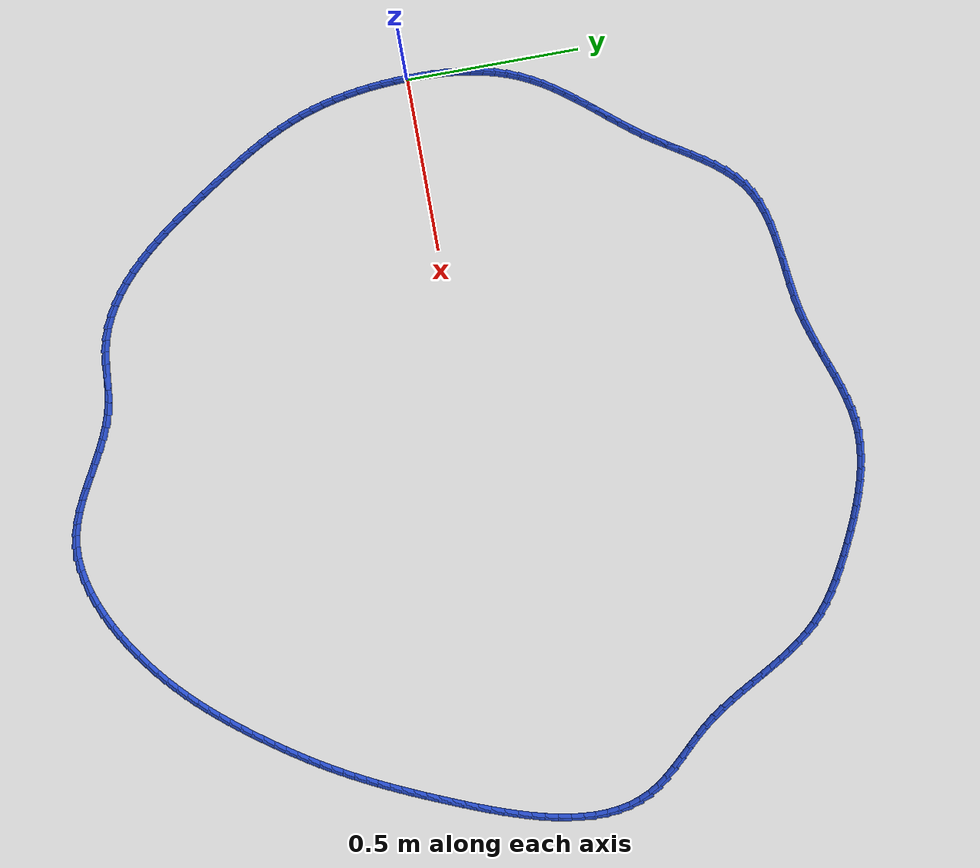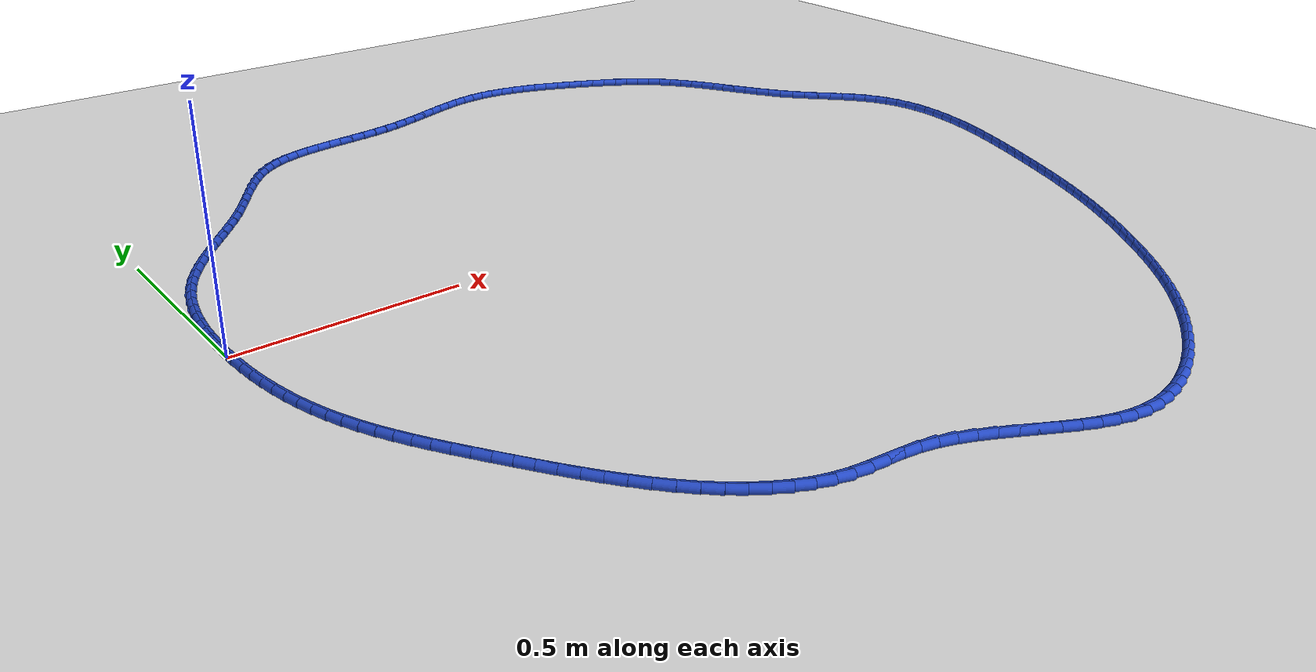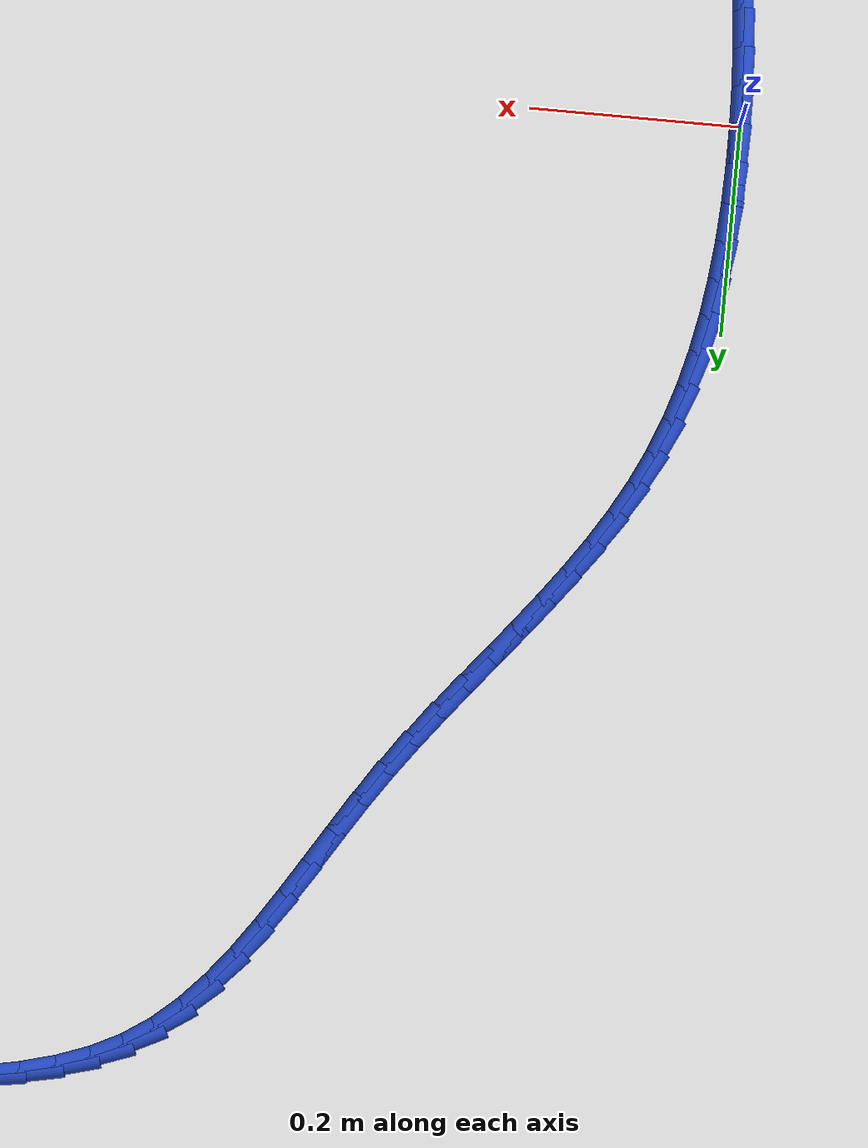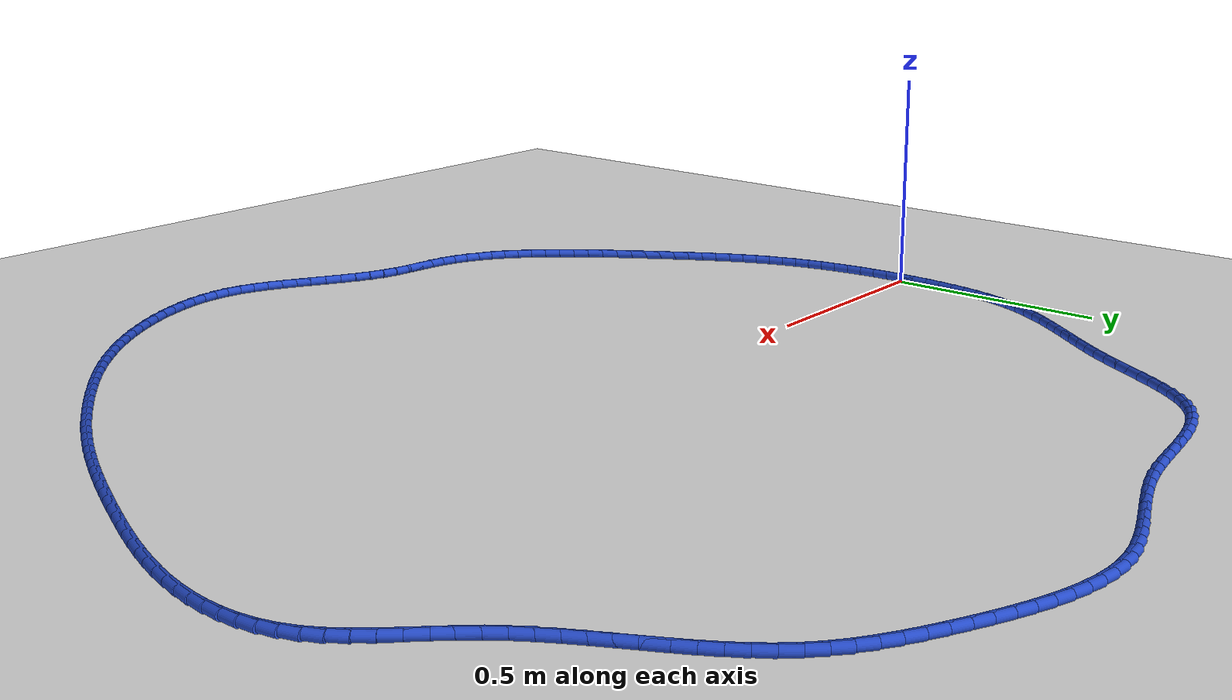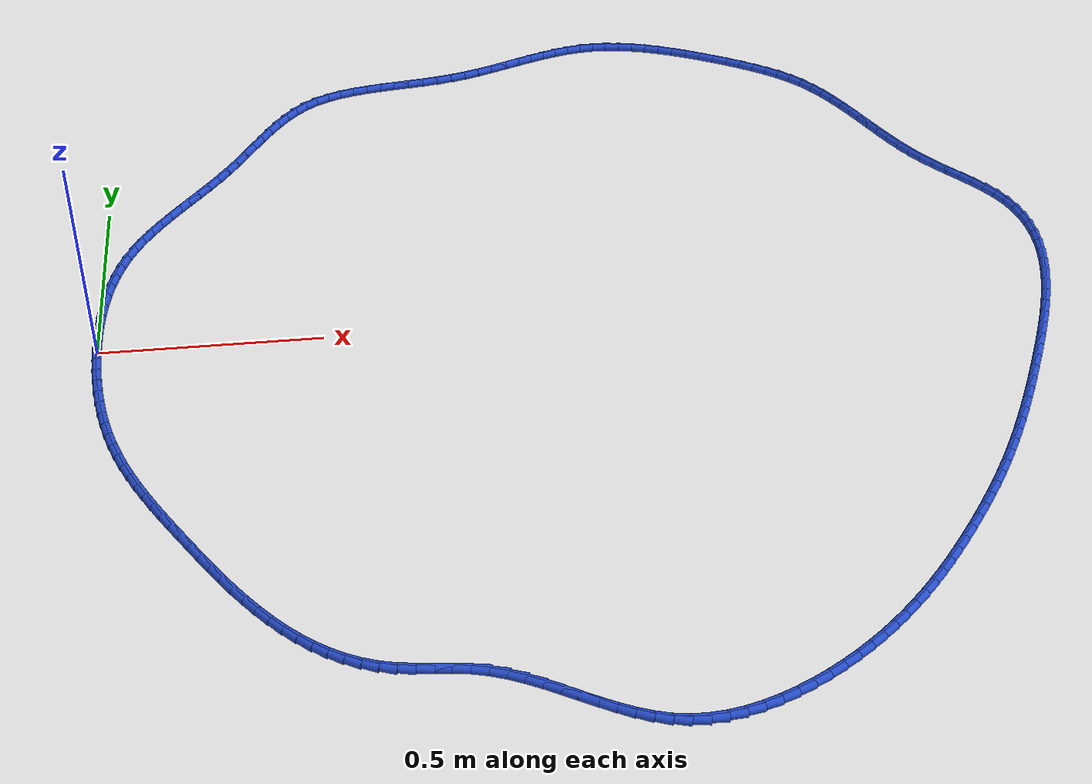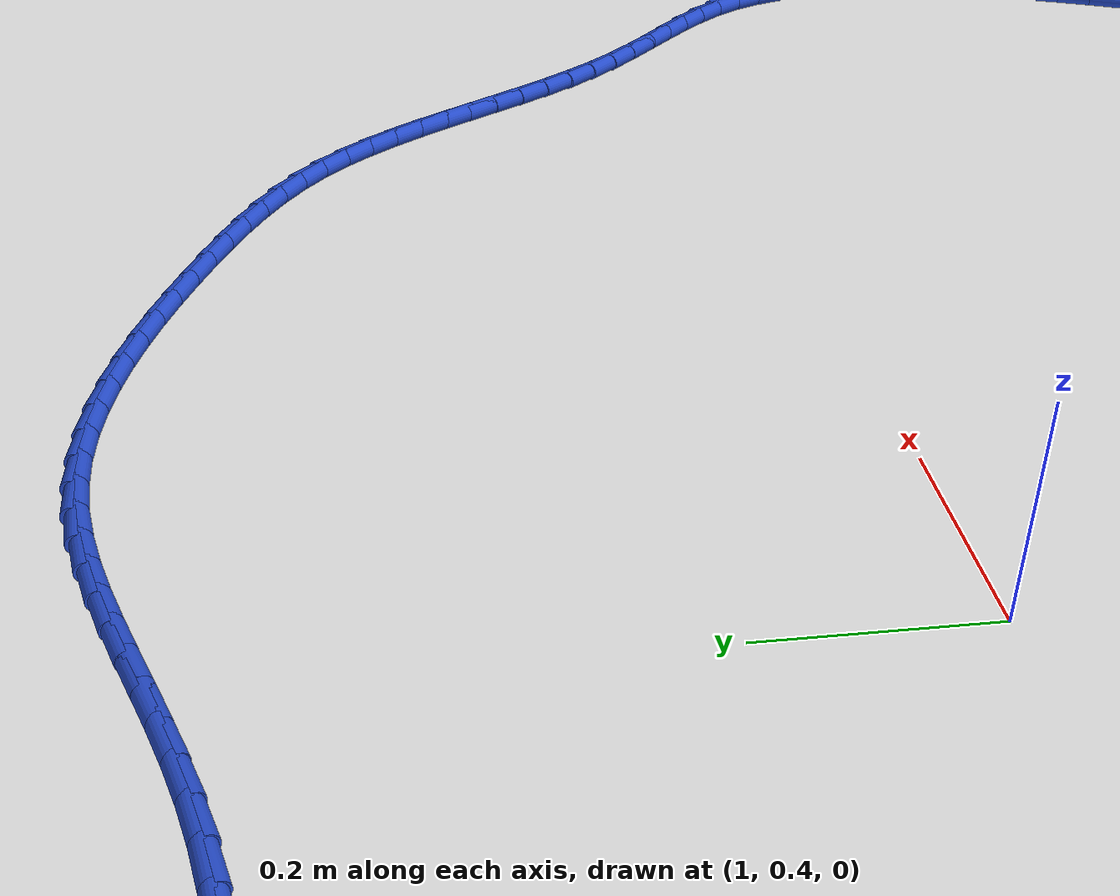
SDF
<sdf version="1.6">
 <world name="default">
  <light name="sun" type="directional">
   <pose>0 0 10 0 -0 0</pose>
   <diffuse>0.8 0.8 0.8 1</diffuse>
   <specular>0.2 0.2 0.2 1</specular>
   <attenuation>
    <range>1000</range>
    <constant>0.9</constant>
    <linear>0.01</linear>
    <quadratic>0.001</quadratic>
   </attenuation>
   <direction>-0.5 0.1 -0.9</direction>
  </light>
  <model name="ground_plane">
   <static>1</static>
   <link name="link">
    <collision name="collision">
     <geometry><plane><normal>0 0 1</normal><size>100 100</size></plane></geometry>
     <surface><friction><ode><mu>100</mu><mu2>50</mu2></ode></friction></surface>
    </collision>
    <visual name="visual">
     <cast_shadows>0</cast_shadows>
     <geometry><plane><normal>0 0 1</normal><size>100 100</size></plane></geometry>
     <material>
      <script><uri>file://media/materials/scripts/gazebo.material</uri><name>Gazebo/WhiteGlow</name></script>
     </material>
    </visual>
   </link>
  </model>
  <gravity>0 0 -9.8</gravity>
  <magnetic_field>6e-06 2.3e-05 -4.2e-05</magnetic_field>
  <atmosphere type="adiabatic"/>
  <physics name="default_physics" default="0" type="ode">
   <max_step_size>0.001</max_step_size>
   <real_time_factor>1</real_time_factor>
   <real_time_update_rate>1000</real_time_update_rate>
  </physics>
  <scene><ambient>0.4 0.4 0.4 1</ambient><background>0.7 0.7 0.7 1</background><shadows>1</shadows></scene>
  <spherical_coordinates>
   <surface_model>EARTH_WGS84</surface_model>
   <latitude_deg>0</latitude_deg>
   <longitude_deg>0</longitude_deg>
   <elevation>0</elevation>
   <heading_deg>0</heading_deg>
  </spherical_coordinates>
  <model name="line">
   <link name="link_0">
    <pose>-8.673617379884035e-19 1.3877787807814457e-17 0.01 0 1.57 -1.5691896120427902</pose>
    <collision name="collision">
     <geometry><cylinder><radius>0.01</radius><length>0.08</length></cylinder></geometry>
    </collision>
    <visual name="visual">
     <material>
      <script><name>Gazebo/Blue</name><uri>file://media/materials/scripts/gazebo.material</uri></script>
     </material>
     <geometry><cylinder><radius>0.01</radius><length>0.08</length></cylinder></geometry>
    </visual>
   </link>
   <link name="link_1">
    <pose>-5.9115855555821446e-05 0.03679296814103423 0.01 0 1.57 1.541697354999295</pose>
    <collision name="collision">
     <geometry><cylinder><radius>0.01</radius><length>0.08</length></cylinder></geometry>
    </collision>
    <visual name="visual">
     <material>
      <script><name>Gazebo/Blue</name><uri>file://media/materials/scripts/gazebo.material</uri></script>
     </material>
     <geometry><cylinder><radius>0.01</radius><length>0.08</length></cylinder></geometry>
    </visual>
   </link>
   <link name="link_2">
    <pose>0.0010114618847792624 0.07357349633872798 0.01 0 1.57 1.5071595748917275</pose>
    <collision name="collision">
     <geometry><cylinder><radius>0.01</radius><length>0.08</length></cylinder></geometry>
    </collision>
    <visual name="visual">
     <material>
      <script><name>Gazebo/Blue</name><uri>file://media/materials/scripts/gazebo.material</uri></script>
     </material>
     <geometry><cylinder><radius>0.01</radius><length>0.08</length></cylinder></geometry>
    </visual>
   </link>
   <link name="link_3">
    <pose>0.0033449624620756143 0.11019305522677555 0.01 0 1.57 1.4684385178057604</pose>
    <collision name="collision">
     <geometry><cylinder><radius>0.01</radius><length>0.08</length></cylinder></geometry>
    </collision>
    <visual name="visual">
     <material>
      <script><name>Gazebo/Blue</name><uri>file://media/materials/scripts/gazebo.material</uri></script>
     </material>
     <geometry><cylinder><radius>0.01</radius><length>0.08</length></cylinder></geometry>
    </visual>
   </link>
   <link name="link_4">
    <pose>0.007074615117403593 0.14650311543887132 0.01 0 1.57 1.4251478518659704</pose>
    <collision name="collision">
     <geometry><cylinder><radius>0.01</radius><length>0.08</length></cylinder></geometry>
    </collision>
    <visual name="visual">
     <material>
      <script><name>Gazebo/Blue</name><uri>file://media/materials/scripts/gazebo.material</uri></script>
     </material>
     <geometry><cylinder><radius>0.01</radius><length>0.08</length></cylinder></geometry>
    </visual>
   </link>
   <link name="link_5">
    <pose>0.012333649091833553 0.18235514760870958 0.01 0 1.57 1.3768801714346215</pose>
    <collision name="collision">
     <geometry><cylinder><radius>0.01</radius><length>0.08</length></cylinder></geometry>
    </collision>
    <visual name="visual">
     <material>
      <script><name>Gazebo/Blue</name><uri>file://media/materials/scripts/gazebo.material</uri></script>
     </material>
     <geometry><cylinder><radius>0.01</radius><length>0.08</length></cylinder></geometry>
    </visual>
   </link>
   <link name="link_6">
    <pose>0.019255293626435868 0.21760062236998456 0.01 0 1.57 1.3232300511538342</pose>
    <collision name="collision">
     <geometry><cylinder><radius>0.01</radius><length>0.08</length></cylinder></geometry>
    </collision>
    <visual name="visual">
     <material>
      <script><name>Gazebo/Blue</name><uri>file://media/materials/scripts/gazebo.material</uri></script>
     </material>
     <geometry><cylinder><radius>0.01</radius><length>0.08</length></cylinder></geometry>
    </visual>
   </link>
   <link name="link_7">
    <pose>0.02797277796228087 0.25209101035639064 0.01 0 1.57 1.2638293466136068</pose>
    <collision name="collision">
     <geometry><cylinder><radius>0.01</radius><length>0.08</length></cylinder></geometry>
    </collision>
    <visual name="visual">
     <material>
      <script><name>Gazebo/Blue</name><uri>file://media/materials/scripts/gazebo.material</uri></script>
     </material>
     <geometry><cylinder><radius>0.01</radius><length>0.08</length></cylinder></geometry>
    </visual>
   </link>
   <link name="link_8">
    <pose>0.03861933134043894 0.28567778220162204 0.01 0 1.57 1.1983975268193925</pose>
    <collision name="collision">
     <geometry><cylinder><radius>0.01</radius><length>0.08</length></cylinder></geometry>
    </collision>
    <visual name="visual">
     <material>
      <script><name>Gazebo/Blue</name><uri>file://media/materials/scripts/gazebo.material</uri></script>
     </material>
     <geometry><cylinder><radius>0.01</radius><length>0.08</length></cylinder></geometry>
    </visual>
   </link>
   <link name="link_9">
    <pose>0.05132818300198046 0.3182124085393733 0.01 0 1.57 1.1280892747481899</pose>
    <collision name="collision">
     <geometry><cylinder><radius>0.01</radius><length>0.08</length></cylinder></geometry>
    </collision>
    <visual name="visual">
     <material>
      <script><name>Gazebo/Blue</name><uri>file://media/materials/scripts/gazebo.material</uri></script>
     </material>
     <geometry><cylinder><radius>0.01</radius><length>0.08</length></cylinder></geometry>
    </visual>
   </link>
   <link name="link_10">
    <pose>0.0661974743667256 0.3495761484289583 0.01 0 1.57 1.0628469063086112</pose>
    <collision name="collision">
     <geometry><cylinder><radius>0.01</radius><length>0.08</length></cylinder></geometry>
    </collision>
    <visual name="visual">
     <material>
      <script><name>Gazebo/Blue</name><uri>file://media/materials/scripts/gazebo.material</uri></script>
     </material>
     <geometry><cylinder><radius>0.01</radius><length>0.08</length></cylinder></geometry>
    </visual>
   </link>
   <link name="link_11">
    <pose>0.08306286624874386 0.3798730984762375 0.01 0 1.57 1.0077809539167577</pose>
    <collision name="collision">
     <geometry><cylinder><radius>0.01</radius><length>0.08</length></cylinder></geometry>
    </collision>
    <visual name="visual">
     <material>
      <script><name>Gazebo/Blue</name><uri>file://media/materials/scripts/gazebo.material</uri></script>
     </material>
     <geometry><cylinder><radius>0.01</radius><length>0.08</length></cylinder></geometry>
    </visual>
   </link>
   <link name="link_12">
    <pose>0.10164112701029362 0.40930829113407907 0.01 0 1.57 0.9632950776394239</pose>
    <collision name="collision">
     <geometry><cylinder><radius>0.01</radius><length>0.08</length></cylinder></geometry>
    </collision>
    <visual name="visual">
     <material>
      <script><name>Gazebo/Blue</name><uri>file://media/materials/scripts/gazebo.material</uri></script>
     </material>
     <geometry><cylinder><radius>0.01</radius><length>0.08</length></cylinder></geometry>
    </visual>
   </link>
   <link name="link_13">
    <pose>0.12164843693284727 0.4380872581169217 0.01 0 1.57 0.9294146926890351</pose>
    <collision name="collision">
     <geometry><cylinder><radius>0.01</radius><length>0.08</length></cylinder></geometry>
    </collision>
    <visual name="visual">
     <material>
      <script><name>Gazebo/Blue</name><uri>file://media/materials/scripts/gazebo.material</uri></script>
     </material>
     <geometry><cylinder><radius>0.01</radius><length>0.08</length></cylinder></geometry>
    </visual>
   </link>
   <link name="link_14">
    <pose>0.14280097629787689 0.4664155311392039 0.01 0 1.57 0.905958699298037</pose>
    <collision name="collision">
     <geometry><cylinder><radius>0.01</radius><length>0.08</length></cylinder></geometry>
    </collision>
    <visual name="visual">
     <material>
      <script><name>Gazebo/Blue</name><uri>file://media/materials/scripts/gazebo.material</uri></script>
     </material>
     <geometry><cylinder><radius>0.01</radius><length>0.08</length></cylinder></geometry>
    </visual>
   </link>
   <link name="link_15">
    <pose>0.16481492538685505 0.4944986419153648 0.01 0 1.57 0.892656306667746</pose>
    <collision name="collision">
     <geometry><cylinder><radius>0.01</radius><length>0.08</length></cylinder></geometry>
    </collision>
    <visual name="visual">
     <material>
      <script><name>Gazebo/Blue</name><uri>file://media/materials/scripts/gazebo.material</uri></script>
     </material>
     <geometry><cylinder><radius>0.01</radius><length>0.08</length></cylinder></geometry>
    </visual>
   </link>
   <link name="link_16">
    <pose>0.18740646448125392 0.5225421221598434 0.01 0 1.57 0.8892235811790805</pose>
    <collision name="collision">
     <geometry><cylinder><radius>0.01</radius><length>0.08</length></cylinder></geometry>
    </collision>
    <visual name="visual">
     <material>
      <script><name>Gazebo/Blue</name><uri>file://media/materials/scripts/gazebo.material</uri></script>
     </material>
     <geometry><cylinder><radius>0.01</radius><length>0.08</length></cylinder></geometry>
    </visual>
   </link>
   <link name="link_17">
    <pose>0.2102917738625458 0.5507515035870779 0.01 0 1.57 0.8954027101737718</pose>
    <collision name="collision">
     <geometry><cylinder><radius>0.01</radius><length>0.08</length></cylinder></geometry>
    </collision>
    <visual name="visual">
     <material>
      <script><name>Gazebo/Blue</name><uri>file://media/materials/scripts/gazebo.material</uri></script>
     </material>
     <geometry><cylinder><radius>0.01</radius><length>0.08</length></cylinder></geometry>
    </visual>
   </link>
   <link name="link_18">
    <pose>0.23318703381220296 0.5793323179115075 0.01 0 1.57 0.9109698212362631</pose>
    <collision name="collision">
     <geometry><cylinder><radius>0.01</radius><length>0.08</length></cylinder></geometry>
    </collision>
    <visual name="visual">
     <material>
      <script><name>Gazebo/Blue</name><uri>file://media/materials/scripts/gazebo.material</uri></script>
     </material>
     <geometry><cylinder><radius>0.01</radius><length>0.08</length></cylinder></geometry>
    </visual>
   </link>
   <link name="link_19">
    <pose>0.2558084246116976 0.6084900968475708 0.01 0 1.57 0.9357166348205601</pose>
    <collision name="collision">
     <geometry><cylinder><radius>0.01</radius><length>0.08</length></cylinder></geometry>
    </collision>
    <visual name="visual">
     <material>
      <script><name>Gazebo/Blue</name><uri>file://media/materials/scripts/gazebo.material</uri></script>
     </material>
     <geometry><cylinder><radius>0.01</radius><length>0.08</length></cylinder></geometry>
    </visual>
   </link>
   <link name="link_20">
    <pose>0.2778721265425023 0.6384303721097069 0.01 0 1.57 0.9688860292136666</pose>
    <collision name="collision">
     <geometry><cylinder><radius>0.01</radius><length>0.08</length></cylinder></geometry>
    </collision>
    <visual name="visual">
     <material>
      <script><name>Gazebo/Blue</name><uri>file://media/materials/scripts/gazebo.material</uri></script>
     </material>
     <geometry><cylinder><radius>0.01</radius><length>0.08</length></cylinder></geometry>
    </visual>
   </link>
   <link name="link_21">
    <pose>0.29910762861970175 0.6693433356759139 0.01 0 1.57 0.9981026038053255</pose>
    <collision name="collision">
     <geometry><cylinder><radius>0.01</radius><length>0.08</length></cylinder></geometry>
    </collision>
    <visual name="visual">
     <material>
      <script><name>Gazebo/Blue</name><uri>file://media/materials/scripts/gazebo.material</uri></script>
     </material>
     <geometry><cylinder><radius>0.01</radius><length>0.08</length></cylinder></geometry>
    </visual>
   </link>
   <link name="link_22">
    <pose>0.3195570271918366 0.7010588661958075 0.01 0 1.57 1.0114778019806516</pose>
    <collision name="collision">
     <geometry><cylinder><radius>0.01</radius><length>0.08</length></cylinder></geometry>
    </collision>
    <visual name="visual">
     <material>
      <script><name>Gazebo/Blue</name><uri>file://media/materials/scripts/gazebo.material</uri></script>
     </material>
     <geometry><cylinder><radius>0.01</radius><length>0.08</length></cylinder></geometry>
    </visual>
   </link>
   <link name="link_23">
    <pose>0.33957868394489893 0.7330423127504555 0.01 0 1.57 1.0087228652466187</pose>
    <collision name="collision">
     <geometry><cylinder><radius>0.01</radius><length>0.08</length></cylinder></geometry>
    </collision>
    <visual name="visual">
     <material>
      <script><name>Gazebo/Blue</name><uri>file://media/materials/scripts/gazebo.material</uri></script>
     </material>
     <geometry><cylinder><radius>0.01</radius><length>0.08</length></cylinder></geometry>
    </visual>
   </link>
   <link name="link_24">
    <pose>0.3595450009303327 0.7647428414006764 0.01 0 1.57 0.9894275158267191</pose>
    <collision name="collision">
     <geometry><cylinder><radius>0.01</radius><length>0.08</length></cylinder></geometry>
    </collision>
    <visual name="visual">
     <material>
      <script><name>Gazebo/Blue</name><uri>file://media/materials/scripts/gazebo.material</uri></script>
     </material>
     <geometry><cylinder><radius>0.01</radius><length>0.08</length></cylinder></geometry>
    </visual>
   </link>
   <link name="link_25">
    <pose>0.3798283801995818 0.7956096182072877 0.01 0 1.57 0.9524779871922515</pose>
    <collision name="collision">
     <geometry><cylinder><radius>0.01</radius><length>0.08</length></cylinder></geometry>
    </collision>
    <visual name="visual">
     <material>
      <script><name>Gazebo/Blue</name><uri>file://media/materials/scripts/gazebo.material</uri></script>
     </material>
     <geometry><cylinder><radius>0.01</radius><length>0.08</length></cylinder></geometry>
    </visual>
   </link>
   <link name="link_26">
    <pose>0.40080122380409017 0.8250918092311078 0.01 0 1.57 0.8961153088186018</pose>
    <collision name="collision">
     <geometry><cylinder><radius>0.01</radius><length>0.08</length></cylinder></geometry>
    </collision>
    <visual name="visual">
     <material>
      <script><name>Gazebo/Blue</name><uri>file://media/materials/scripts/gazebo.material</uri></script>
     </material>
     <geometry><cylinder><radius>0.01</radius><length>0.08</length></cylinder></geometry>
    </visual>
   </link>
   <link name="link_27">
    <pose>0.42283593379530154 0.8526385805329542 0.01 0 1.57 0.8181817099947388</pose>
    <collision name="collision">
     <geometry><cylinder><radius>0.01</radius><length>0.08</length></cylinder></geometry>
    </collision>
    <visual name="visual">
     <material>
      <script><name>Gazebo/Blue</name><uri>file://media/materials/scripts/gazebo.material</uri></script>
     </material>
     <geometry><cylinder><radius>0.01</radius><length>0.08</length></cylinder></geometry>
    </visual>
   </link>
   <link name="link_28">
    <pose>0.44630491222466007 0.8776990981736454 0.01 0 1.57 0.7167476057622834</pose>
    <collision name="collision">
     <geometry><cylinder><radius>0.01</radius><length>0.08</length></cylinder></geometry>
    </collision>
    <visual name="visual">
     <material>
      <script><name>Gazebo/Blue</name><uri>file://media/materials/scripts/gazebo.material</uri></script>
     </material>
     <geometry><cylinder><radius>0.01</radius><length>0.08</length></cylinder></geometry>
    </visual>
   </link>
   <link name="link_29">
    <pose>0.47158056114360947 0.8997225282139991 0.01 0 1.57 0.5917236856192647</pose>
    <collision name="collision">
     <geometry><cylinder><radius>0.01</radius><length>0.08</length></cylinder></geometry>
    </collision>
    <visual name="visual">
     <material>
      <script><name>Gazebo/Blue</name><uri>file://media/materials/scripts/gazebo.material</uri></script>
     </material>
     <geometry><cylinder><radius>0.01</radius><length>0.08</length></cylinder></geometry>
    </visual>
   </link>
   <link name="link_30">
    <pose>0.4990286189794824 0.9181691314795822 0.01 0 1.57 0.4617291212682363</pose>
    <collision name="collision">
     <geometry><cylinder><radius>0.01</radius><length>0.08</length></cylinder></geometry>
    </collision>
    <visual name="visual">
     <material>
      <script><name>Gazebo/Blue</name><uri>file://media/materials/scripts/gazebo.material</uri></script>
     </material>
     <geometry><cylinder><radius>0.01</radius><length>0.08</length></cylinder></geometry>
    </visual>
   </link>
   <link name="link_31">
    <pose>0.5287414357863561 0.932954353487616 0.01 0 1.57 0.35197722542888493</pose>
    <collision name="collision">
     <geometry><cylinder><radius>0.01</radius><length>0.08</length></cylinder></geometry>
    </collision>
    <visual name="visual">
     <material>
      <script><name>Gazebo/Blue</name><uri>file://media/materials/scripts/gazebo.material</uri></script>
     </material>
     <geometry><cylinder><radius>0.01</radius><length>0.08</length></cylinder></geometry>
    </visual>
   </link>
   <link name="link_32">
    <pose>0.5604476944106817 0.944599136411219 0.01 0 1.57 0.26506040477492726</pose>
    <collision name="collision">
     <geometry><cylinder><radius>0.01</radius><length>0.08</length></cylinder></geometry>
    </collision>
    <visual name="visual">
     <material>
      <script><name>Gazebo/Blue</name><uri>file://media/materials/scripts/gazebo.material</uri></script>
     </material>
     <geometry><cylinder><radius>0.01</radius><length>0.08</length></cylinder></geometry>
    </visual>
   </link>
   <link name="link_33">
    <pose>0.5938508961949553 0.953666348987455 0.01 0 1.57 0.1999299701820391</pose>
    <collision name="collision">
     <geometry><cylinder><radius>0.01</radius><length>0.08</length></cylinder></geometry>
    </collision>
    <visual name="visual">
     <material>
      <script><name>Gazebo/Blue</name><uri>file://media/materials/scripts/gazebo.material</uri></script>
     </material>
     <geometry><cylinder><radius>0.01</radius><length>0.08</length></cylinder></geometry>
    </visual>
   </link>
   <link name="link_34">
    <pose>0.6286545424816737 0.9607188599533883 0.01 0 1.57 0.15472805098623982</pose>
    <collision name="collision">
     <geometry><cylinder><radius>0.01</radius><length>0.08</length></cylinder></geometry>
    </collision>
    <visual name="visual">
     <material>
      <script><name>Gazebo/Blue</name><uri>file://media/materials/scripts/gazebo.material</uri></script>
     </material>
     <geometry><cylinder><radius>0.01</radius><length>0.08</length></cylinder></geometry>
    </visual>
   </link>
   <link name="link_35">
    <pose>0.6645621346133327 0.966319538046083 0.01 0 1.57 0.12763436382105578</pose>
    <collision name="collision">
     <geometry><cylinder><radius>0.01</radius><length>0.08</length></cylinder></geometry>
    </collision>
    <visual name="visual">
     <material>
      <script><name>Gazebo/Blue</name><uri>file://media/materials/scripts/gazebo.material</uri></script>
     </material>
     <geometry><cylinder><radius>0.01</radius><length>0.08</length></cylinder></geometry>
    </visual>
   </link>
   <link name="link_36">
    <pose>0.7012771739324284 0.9710312520026025 0.01 0 1.57 0.11727011874736659</pose>
    <collision name="collision">
     <geometry><cylinder><radius>0.01</radius><length>0.08</length></cylinder></geometry>
    </collision>
    <visual name="visual">
     <material>
      <script><name>Gazebo/Blue</name><uri>file://media/materials/scripts/gazebo.material</uri></script>
     </material>
     <geometry><cylinder><radius>0.01</radius><length>0.08</length></cylinder></geometry>
    </visual>
   </link>
   <link name="link_37">
    <pose>0.7385031617814575 0.975416870560012 0.01 0 1.57 0.12283828097464813</pose>
    <collision name="collision">
     <geometry><cylinder><radius>0.01</radius><length>0.08</length></cylinder></geometry>
    </collision>
    <visual name="visual">
     <material>
      <script><name>Gazebo/Blue</name><uri>file://media/materials/scripts/gazebo.material</uri></script>
     </material>
     <geometry><cylinder><radius>0.01</radius><length>0.08</length></cylinder></geometry>
    </visual>
   </link>
   <link name="link_38">
    <pose>0.7759435995029157 0.9800392624553746 0.01 0 1.57 0.14412927345510365</pose>
    <collision name="collision">
     <geometry><cylinder><radius>0.01</radius><length>0.08</length></cylinder></geometry>
    </collision>
    <visual name="visual">
     <material>
      <script><name>Gazebo/Blue</name><uri>file://media/materials/scripts/gazebo.material</uri></script>
     </material>
     <geometry><cylinder><radius>0.01</radius><length>0.08</length></cylinder></geometry>
    </visual>
   </link>
   <link name="link_39">
    <pose>0.8133019884392998 0.9854612964257548 0.01 0 1.57 0.18144815492154917</pose>
    <collision name="collision">
     <geometry><cylinder><radius>0.01</radius><length>0.08</length></cylinder></geometry>
    </collision>
    <visual name="visual">
     <material>
      <script><name>Gazebo/Blue</name><uri>file://media/materials/scripts/gazebo.material</uri></script>
     </material>
     <geometry><cylinder><radius>0.01</radius><length>0.08</length></cylinder></geometry>
    </visual>
   </link>
   <link name="link_40">
    <pose>0.8502818299331054 0.9922458412082165 0.01 0 1.57 0.23360202607498107</pose>
    <collision name="collision">
     <geometry><cylinder><radius>0.01</radius><length>0.08</length></cylinder></geometry>
    </collision>
    <visual name="visual">
     <material>
      <script><name>Gazebo/Blue</name><uri>file://media/materials/scripts/gazebo.material</uri></script>
     </material>
     <geometry><cylinder><radius>0.01</radius><length>0.08</length></cylinder></geometry>
    </visual>
   </link>
   <link name="link_41">
    <pose>0.8866109141577839 1.0008902046198174 0.01 0 1.57 0.2827558952058957</pose>
    <collision name="collision">
     <geometry><cylinder><radius>0.01</radius><length>0.08</length></cylinder></geometry>
    </collision>
    <visual name="visual">
     <material>
      <script><name>Gazebo/Blue</name><uri>file://media/materials/scripts/gazebo.material</uri></script>
     </material>
     <geometry><cylinder><radius>0.01</radius><length>0.08</length></cylinder></geometry>
    </visual>
   </link>
   <link name="link_42">
    <pose>0.9222560402752632 1.011246556422014 0.01 0 1.57 0.31830524650128084</pose>
    <collision name="collision">
     <geometry><cylinder><radius>0.01</radius><length>0.08</length></cylinder></geometry>
    </collision>
    <visual name="visual">
     <material>
      <script><name>Gazebo/Blue</name><uri>file://media/materials/scripts/gazebo.material</uri></script>
     </material>
     <geometry><cylinder><radius>0.01</radius><length>0.08</length></cylinder></geometry>
    </visual>
   </link>
   <link name="link_43">
    <pose>0.9573198431801015 1.0228004157285768 0.01 0 1.57 0.3399505594564648</pose>
    <collision name="collision">
     <geometry><cylinder><radius>0.01</radius><length>0.08</length></cylinder></geometry>
    </collision>
    <visual name="visual">
     <material>
      <script><name>Gazebo/Blue</name><uri>file://media/materials/scripts/gazebo.material</uri></script>
     </material>
     <geometry><cylinder><radius>0.01</radius><length>0.08</length></cylinder></geometry>
    </visual>
   </link>
   <link name="link_44">
    <pose>0.9919065232600868 1.0350330760412396 0.01 0 1.57 0.3475155464305909</pose>
    <collision name="collision">
     <geometry><cylinder><radius>0.01</radius><length>0.08</length></cylinder></geometry>
    </collision>
    <visual name="visual">
     <material>
      <script><name>Gazebo/Blue</name><uri>file://media/materials/scripts/gazebo.material</uri></script>
     </material>
     <geometry><cylinder><radius>0.01</radius><length>0.08</length></cylinder></geometry>
    </visual>
   </link>
   <link name="link_45">
    <pose>1.0261202809030063 1.0474258308617361 0.01 0 1.57 0.34069451706028403</pose>
    <collision name="collision">
     <geometry><cylinder><radius>0.01</radius><length>0.08</length></cylinder></geometry>
    </collision>
    <visual name="visual">
     <material>
      <script><name>Gazebo/Blue</name><uri>file://media/materials/scripts/gazebo.material</uri></script>
     </material>
     <geometry><cylinder><radius>0.01</radius><length>0.08</length></cylinder></geometry>
    </visual>
   </link>
   <link name="link_46">
    <pose>1.060065316496648 1.0594599736917993 0.01 0 1.57 0.3189946021658939</pose>
    <collision name="collision">
     <geometry><cylinder><radius>0.01</radius><length>0.08</length></cylinder></geometry>
    </collision>
    <visual name="visual">
     <material>
      <script><name>Gazebo/Blue</name><uri>file://media/materials/scripts/gazebo.material</uri></script>
     </material>
     <geometry><cylinder><radius>0.01</radius><length>0.08</length></cylinder></geometry>
    </visual>
   </link>
   <link name="link_47">
    <pose>1.0938458304287992 1.0706167980331625 0.01 0 1.57 0.2817634108245658</pose>
    <collision name="collision">
     <geometry><cylinder><radius>0.01</radius><length>0.08</length></cylinder></geometry>
    </collision>
    <visual name="visual">
     <material>
      <script><name>Gazebo/Blue</name><uri>file://media/materials/scripts/gazebo.material</uri></script>
     </material>
     <geometry><cylinder><radius>0.01</radius><length>0.08</length></cylinder></geometry>
    </visual>
   </link>
   <link name="link_48">
    <pose>1.1275660230872484 1.0803775973875602 0.01 0 1.57 0.2283268708331586</pose>
    <collision name="collision">
     <geometry><cylinder><radius>0.01</radius><length>0.08</length></cylinder></geometry>
    </collision>
    <visual name="visual">
     <material>
      <script><name>Gazebo/Blue</name><uri>file://media/materials/scripts/gazebo.material</uri></script>
     </material>
     <geometry><cylinder><radius>0.01</radius><length>0.08</length></cylinder></geometry>
    </visual>
   </link>
   <link name="link_49">
    <pose>1.1613300948597822 1.0882236652567254 0.01 0 1.57 0.1582724267237799</pose>
    <collision name="collision">
     <geometry><cylinder><radius>0.01</radius><length>0.08</length></cylinder></geometry>
    </collision>
    <visual name="visual">
     <material>
      <script><name>Gazebo/Blue</name><uri>file://media/materials/scripts/gazebo.material</uri></script>
     </material>
     <geometry><cylinder><radius>0.01</radius><length>0.08</length></cylinder></geometry>
    </visual>
   </link>
   <link name="link_50">
    <pose>1.1952422461341896 1.093636295142392 0.01 0 1.57 0.07204811251900972</pose>
    <collision name="collision">
     <geometry><cylinder><radius>0.01</radius><length>0.08</length></cylinder></geometry>
    </collision>
    <visual name="visual">
     <material>
      <script><name>Gazebo/Blue</name><uri>file://media/materials/scripts/gazebo.material</uri></script>
     </material>
     <geometry><cylinder><radius>0.01</radius><length>0.08</length></cylinder></geometry>
    </visual>
   </link>
   <link name="link_51">
    <pose>1.2294054708929467 1.0961019588439644 0.01 0 1.57 -0.02013495659202029</pose>
    <collision name="collision">
     <geometry><cylinder><radius>0.01</radius><length>0.08</length></cylinder></geometry>
    </collision>
    <visual name="visual">
     <material>
      <script><name>Gazebo/Blue</name><uri>file://media/materials/scripts/gazebo.material</uri></script>
     </material>
     <geometry><cylinder><radius>0.01</radius><length>0.08</length></cylinder></geometry>
    </visual>
   </link>
   <link name="link_52">
    <pose>1.2638526042681257 1.0954082735623876 0.01 0 1.57 -0.10362141719256841</pose>
    <collision name="collision">
     <geometry><cylinder><radius>0.01</radius><length>0.08</length></cylinder></geometry>
    </collision>
    <visual name="visual">
     <material>
      <script><name>Gazebo/Blue</name><uri>file://media/materials/scripts/gazebo.material</uri></script>
     </material>
     <geometry><cylinder><radius>0.01</radius><length>0.08</length></cylinder></geometry>
    </visual>
   </link>
   <link name="link_53">
    <pose>1.2985089958736835 1.091804220522175 0.01 0 1.57 -0.17713580263408576</pose>
    <collision name="collision">
     <geometry><cylinder><radius>0.01</radius><length>0.08</length></cylinder></geometry>
    </collision>
    <visual name="visual">
     <material>
      <script><name>Gazebo/Blue</name><uri>file://media/materials/scripts/gazebo.material</uri></script>
     </material>
     <geometry><cylinder><radius>0.01</radius><length>0.08</length></cylinder></geometry>
    </visual>
   </link>
   <link name="link_54">
    <pose>1.3332908950506261 1.0855778423825249 0.01 0 1.57 -0.24104907224749242</pose>
    <collision name="collision">
     <geometry><cylinder><radius>0.01</radius><length>0.08</length></cylinder></geometry>
    </collision>
    <visual name="visual">
     <material>
      <script><name>Gazebo/Blue</name><uri>file://media/materials/scripts/gazebo.material</uri></script>
     </material>
     <geometry><cylinder><radius>0.01</radius><length>0.08</length></cylinder></geometry>
    </visual>
   </link>
   <link name="link_55">
    <pose>1.3681145511399577 1.0770171818026344 0.01 0 1.57 -0.2959979831827438</pose>
    <collision name="collision">
     <geometry><cylinder><radius>0.01</radius><length>0.08</length></cylinder></geometry>
    </collision>
    <visual name="visual">
     <material>
      <script><name>Gazebo/Blue</name><uri>file://media/materials/scripts/gazebo.material</uri></script>
     </material>
     <geometry><cylinder><radius>0.01</radius><length>0.08</length></cylinder></geometry>
    </visual>
   </link>
   <link name="link_56">
    <pose>1.402896213482683 1.066410281441702 0.01 0 1.57 -0.3427164041190062</pose>
    <collision name="collision">
     <geometry><cylinder><radius>0.01</radius><length>0.08</length></cylinder></geometry>
    </collision>
    <visual name="visual">
     <material>
      <script><name>Gazebo/Blue</name><uri>file://media/materials/scripts/gazebo.material</uri></script>
     </material>
     <geometry><cylinder><radius>0.01</radius><length>0.08</length></cylinder></geometry>
    </visual>
   </link>
   <link name="link_57">
    <pose>1.437552131419807 1.0540451839589244 0.01 0 1.57 -0.381924136392617</pose>
    <collision name="collision">
     <geometry><cylinder><radius>0.01</radius><length>0.08</length></cylinder></geometry>
    </collision>
    <visual name="visual">
     <material>
      <script><name>Gazebo/Blue</name><uri>file://media/materials/scripts/gazebo.material</uri></script>
     </material>
     <geometry><cylinder><radius>0.01</radius><length>0.08</length></cylinder></geometry>
    </visual>
   </link>
   <link name="link_58">
    <pose>1.4719985542923344 1.0402099320135 0.01 0 1.57 -0.4142607019821717</pose>
    <collision name="collision">
     <geometry><cylinder><radius>0.01</radius><length>0.08</length></cylinder></geometry>
    </collision>
    <visual name="visual">
     <material>
      <script><name>Gazebo/Blue</name><uri>file://media/materials/scripts/gazebo.material</uri></script>
     </material>
     <geometry><cylinder><radius>0.01</radius><length>0.08</length></cylinder></geometry>
    </visual>
   </link>
   <link name="link_59">
    <pose>1.5061517314412687 1.0251925682646261 0.01 0 1.57 -0.4402487389170883</pose>
    <collision name="collision">
     <geometry><cylinder><radius>0.01</radius><length>0.08</length></cylinder></geometry>
    </collision>
    <visual name="visual">
     <material>
      <script><name>Gazebo/Blue</name><uri>file://media/materials/scripts/gazebo.material</uri></script>
     </material>
     <geometry><cylinder><radius>0.01</radius><length>0.08</length></cylinder></geometry>
    </visual>
   </link>
   <link name="link_60">
    <pose>1.5399279122076168 1.0092811353715005 0.01 0 1.57 -0.46039853660515717</pose>
    <collision name="collision">
     <geometry><cylinder><radius>0.01</radius><length>0.08</length></cylinder></geometry>
    </collision>
    <visual name="visual">
     <material>
      <script><name>Gazebo/Blue</name><uri>file://media/materials/scripts/gazebo.material</uri></script>
     </material>
     <geometry><cylinder><radius>0.01</radius><length>0.08</length></cylinder></geometry>
    </visual>
   </link>
   <link name="link_61">
    <pose>1.5732417772264704 0.9927592828441077 0.01 0 1.57 -0.48114997031188195</pose>
    <collision name="collision">
     <geometry><cylinder><radius>0.01</radius><length>0.08</length></cylinder></geometry>
    </collision>
    <visual name="visual">
     <material>
      <script><name>Gazebo/Blue</name><uri>file://media/materials/scripts/gazebo.material</uri></script>
     </material>
     <geometry><cylinder><radius>0.01</radius><length>0.08</length></cylinder></geometry>
    </visual>
   </link>
   <link name="link_62">
    <pose>1.6059304304812811 0.9756934073577417 0.01 0 1.57 -0.5117849745100247</pose>
    <collision name="collision">
     <geometry><cylinder><radius>0.01</radius><length>0.08</length></cylinder></geometry>
    </collision>
    <visual name="visual">
     <material>
      <script><name>Gazebo/Blue</name><uri>file://media/materials/scripts/gazebo.material</uri></script>
     </material>
     <geometry><cylinder><radius>0.01</radius><length>0.08</length></cylinder></geometry>
    </visual>
   </link>
   <link name="link_63">
    <pose>1.6377193885459844 0.9578374058790808 0.01 0 1.57 -0.5535942170495342</pose>
    <collision name="collision">
     <geometry><cylinder><radius>0.01</radius><length>0.08</length></cylinder></geometry>
    </collision>
    <visual name="visual">
     <material>
      <script><name>Gazebo/Blue</name><uri>file://media/materials/scripts/gazebo.material</uri></script>
     </material>
     <geometry><cylinder><radius>0.01</radius><length>0.08</length></cylinder></geometry>
    </visual>
   </link>
   <link name="link_64">
    <pose>1.6683255140625266 0.9389209401027706 0.01 0 1.57 -0.6072434281945313</pose>
    <collision name="collision">
     <geometry><cylinder><radius>0.01</radius><length>0.08</length></cylinder></geometry>
    </collision>
    <visual name="visual">
     <material>
      <script><name>Gazebo/Blue</name><uri>file://media/materials/scripts/gazebo.material</uri></script>
     </material>
     <geometry><cylinder><radius>0.01</radius><length>0.08</length></cylinder></geometry>
    </visual>
   </link>
   <link name="link_65">
    <pose>1.697465669672853 0.9186736717234572 0.01 0 1.57 -0.6733050236396557</pose>
    <collision name="collision">
     <geometry><cylinder><radius>0.01</radius><length>0.08</length></cylinder></geometry>
    </collision>
    <visual name="visual">
     <material>
      <script><name>Gazebo/Blue</name><uri>file://media/materials/scripts/gazebo.material</uri></script>
     </material>
     <geometry><cylinder><radius>0.01</radius><length>0.08</length></cylinder></geometry>
    </visual>
   </link>
   <link name="link_66">
    <pose>1.724856718018909 0.8968252624357862 0.01 0 1.57 -0.7518722668167446</pose>
    <collision name="collision">
     <geometry><cylinder><radius>0.01</radius><length>0.08</length></cylinder></geometry>
    </collision>
    <visual name="visual">
     <material>
      <script><name>Gazebo/Blue</name><uri>file://media/materials/scripts/gazebo.material</uri></script>
     </material>
     <geometry><cylinder><radius>0.01</radius><length>0.08</length></cylinder></geometry>
    </visual>
   </link>
   <link name="link_67">
    <pose>1.750219316303033 0.8731087036503689 0.01 0 1.57 -0.8337166668977843</pose>
    <collision name="collision">
     <geometry><cylinder><radius>0.01</radius><length>0.08</length></cylinder></geometry>
    </collision>
    <visual name="visual">
     <material>
      <script><name>Gazebo/Blue</name><uri>file://media/materials/scripts/gazebo.material</uri></script>
     </material>
     <geometry><cylinder><radius>0.01</radius><length>0.08</length></cylinder></geometry>
    </visual>
   </link>
   <link name="link_68">
    <pose>1.7735034813660606 0.8474582492091055 0.01 0 1.57 -0.904082668616848</pose>
    <collision name="collision">
     <geometry><cylinder><radius>0.01</radius><length>0.08</length></cylinder></geometry>
    </collision>
    <visual name="visual">
     <material>
      <script><name>Gazebo/Blue</name><uri>file://media/materials/scripts/gazebo.material</uri></script>
     </material>
     <geometry><cylinder><radius>0.01</radius><length>0.08</length></cylinder></geometry>
    </visual>
   </link>
   <link name="link_69">
    <pose>1.7950157103510191 0.8201209634064917 0.01 0 1.57 -0.9611791766321709</pose>
    <collision name="collision">
     <geometry><cylinder><radius>0.01</radius><length>0.08</length></cylinder></geometry>
    </collision>
    <visual name="visual">
     <material>
      <script><name>Gazebo/Blue</name><uri>file://media/materials/scripts/gazebo.material</uri></script>
     </material>
     <geometry><cylinder><radius>0.01</radius><length>0.08</length></cylinder></geometry>
    </visual>
   </link>
   <link name="link_70">
    <pose>1.8150932793610037 0.7913709189870546 0.01 0 1.57 -1.0050182355404382</pose>
    <collision name="collision">
     <geometry><cylinder><radius>0.01</radius><length>0.08</length></cylinder></geometry>
    </collision>
    <visual name="visual">
     <material>
      <script><name>Gazebo/Blue</name><uri>file://media/materials/scripts/gazebo.material</uri></script>
     </material>
     <geometry><cylinder><radius>0.01</radius><length>0.08</length></cylinder></geometry>
    </visual>
   </link>
   <link name="link_71">
    <pose>1.8340734644991106 0.7614821886953218 0.01 0 1.57 -1.035940557369381</pose>
    <collision name="collision">
     <geometry><cylinder><radius>0.01</radius><length>0.08</length></cylinder></geometry>
    </collision>
    <visual name="visual">
     <material>
      <script><name>Gazebo/Blue</name><uri>file://media/materials/scripts/gazebo.material</uri></script>
     </material>
     <geometry><cylinder><radius>0.01</radius><length>0.08</length></cylinder></geometry>
    </visual>
   </link>
   <link name="link_72">
    <pose>1.8522935418684334 0.7307288452758207 0.01 0 1.57 -1.0543853253514919</pose>
    <collision name="collision">
     <geometry><cylinder><radius>0.01</radius><length>0.08</length></cylinder></geometry>
    </collision>
    <visual name="visual">
     <material>
      <script><name>Gazebo/Blue</name><uri>file://media/materials/scripts/gazebo.material</uri></script>
     </material>
     <geometry><cylinder><radius>0.01</radius><length>0.08</length></cylinder></geometry>
    </visual>
   </link>
   <link name="link_73">
    <pose>1.8700907875720687 0.6993849614730793 0.01 0 1.57 -1.0607434821498594</pose>
    <collision name="collision">
     <geometry><cylinder><radius>0.01</radius><length>0.08</length></cylinder></geometry>
    </collision>
    <visual name="visual">
     <material>
      <script><name>Gazebo/Blue</name><uri>file://media/materials/scripts/gazebo.material</uri></script>
     </material>
     <geometry><cylinder><radius>0.01</radius><length>0.08</length></cylinder></geometry>
    </visual>
   </link>
   <link name="link_74">
    <pose>1.8878024777131106 0.6677246100316243 0.01 0 1.57 -1.0552826306442307</pose>
    <collision name="collision">
     <geometry><cylinder><radius>0.01</radius><length>0.08</length></cylinder></geometry>
    </collision>
    <visual name="visual">
     <material>
      <script><name>Gazebo/Blue</name><uri>file://media/materials/scripts/gazebo.material</uri></script>
     </material>
     <geometry><cylinder><radius>0.01</radius><length>0.08</length></cylinder></geometry>
    </visual>
   </link>
   <link name="link_75">
    <pose>1.9057658883946544 0.6360218636959831 0.01 0 1.57 -1.038128180372248</pose>
    <collision name="collision">
     <geometry><cylinder><radius>0.01</radius><length>0.08</length></cylinder></geometry>
    </collision>
    <visual name="visual">
     <material>
      <script><name>Gazebo/Blue</name><uri>file://media/materials/scripts/gazebo.material</uri></script>
     </material>
     <geometry><cylinder><radius>0.01</radius><length>0.08</length></cylinder></geometry>
    </visual>
   </link>
   <link name="link_76">
    <pose>1.924318295719795 0.6045507952106839 0.01 0 1.57 -1.0092911813417413</pose>
    <collision name="collision">
     <geometry><cylinder><radius>0.01</radius><length>0.08</length></cylinder></geometry>
    </collision>
    <visual name="visual">
     <material>
      <script><name>Gazebo/Blue</name><uri>file://media/materials/scripts/gazebo.material</uri></script>
     </material>
     <geometry><cylinder><radius>0.01</radius><length>0.08</length></cylinder></geometry>
    </visual>
   </link>
   <link name="link_77">
    <pose>1.9437969757916285 0.5735854773202534 0.01 0 1.57 -0.9687406918086677</pose>
    <collision name="collision">
     <geometry><cylinder><radius>0.01</radius><length>0.08</length></cylinder></geometry>
    </collision>
    <visual name="visual">
     <material>
      <script><name>Gazebo/Blue</name><uri>file://media/materials/scripts/gazebo.material</uri></script>
     </material>
     <geometry><cylinder><radius>0.01</radius><length>0.08</length></cylinder></geometry>
    </visual>
   </link>
   <link name="link_78">
    <pose>1.96453920471325 0.5433999827692196 0.01 0 1.57 -0.916523797508042</pose>
    <collision name="collision">
     <geometry><cylinder><radius>0.01</radius><length>0.08</length></cylinder></geometry>
    </collision>
    <visual name="visual">
     <material>
      <script><name>Gazebo/Blue</name><uri>file://media/materials/scripts/gazebo.material</uri></script>
     </material>
     <geometry><cylinder><radius>0.01</radius><length>0.08</length></cylinder></geometry>
    </visual>
   </link>
   <link name="link_79">
    <pose>1.9868822255222307 0.5142683651235626 0.01 0 1.57 -0.8601016796847668</pose>
    <collision name="collision">
     <geometry><cylinder><radius>0.01</radius><length>0.08</length></cylinder></geometry>
    </collision>
    <visual name="visual">
     <material>
      <script><name>Gazebo/Blue</name><uri>file://media/materials/scripts/gazebo.material</uri></script>
     </material>
     <geometry><cylinder><radius>0.01</radius><length>0.08</length></cylinder></geometry>
    </visual>
   </link>
   <link name="link_80">
    <pose>2.0109302387920547 0.486329509486581 0.01 0 1.57 -0.8237319674466933</pose>
    <collision name="collision">
     <geometry><cylinder><radius>0.01</radius><length>0.08</length></cylinder></geometry>
    </collision>
    <visual name="visual">
     <material>
      <script><name>Gazebo/Blue</name><uri>file://media/materials/scripts/gazebo.material</uri></script>
     </material>
     <geometry><cylinder><radius>0.01</radius><length>0.08</length></cylinder></geometry>
    </visual>
   </link>
   <link name="link_81">
    <pose>2.0359966893969785 0.45926364964821725 0.01 0 1.57 -0.8119936177274889</pose>
    <collision name="collision">
     <geometry><cylinder><radius>0.01</radius><length>0.08</length></cylinder></geometry>
    </collision>
    <visual name="visual">
     <material>
      <script><name>Gazebo/Blue</name><uri>file://media/materials/scripts/gazebo.material</uri></script>
     </material>
     <geometry><cylinder><radius>0.01</radius><length>0.08</length></cylinder></geometry>
    </visual>
   </link>
   <link name="link_82">
    <pose>2.061227459555405 0.43265383030164284 0.01 0 1.57 -0.825089583868936</pose>
    <collision name="collision">
     <geometry><cylinder><radius>0.01</radius><length>0.08</length></cylinder></geometry>
    </collision>
    <visual name="visual">
     <material>
      <script><name>Gazebo/Blue</name><uri>file://media/materials/scripts/gazebo.material</uri></script>
     </material>
     <geometry><cylinder><radius>0.01</radius><length>0.08</length></cylinder></geometry>
    </visual>
   </link>
   <link name="link_83">
    <pose>2.085768431485741 0.40608309614003013 0.01 0 1.57 -0.8643506545480446</pose>
    <collision name="collision">
     <geometry><cylinder><radius>0.01</radius><length>0.08</length></cylinder></geometry>
    </collision>
    <visual name="visual">
     <material>
      <script><name>Gazebo/Blue</name><uri>file://media/materials/scripts/gazebo.material</uri></script>
     </material>
     <geometry><cylinder><radius>0.01</radius><length>0.08</length></cylinder></geometry>
    </visual>
   </link>
   <link name="link_84">
    <pose>2.108765487406393 0.37913449185655046 0.01 0 1.57 -0.9321235466764143</pose>
    <collision name="collision">
     <geometry><cylinder><radius>0.01</radius><length>0.08</length></cylinder></geometry>
    </collision>
    <visual name="visual">
     <material>
      <script><name>Gazebo/Blue</name><uri>file://media/materials/scripts/gazebo.material</uri></script>
     </material>
     <geometry><cylinder><radius>0.01</radius><length>0.08</length></cylinder></geometry>
    </visual>
   </link>
   <link name="link_85">
    <pose>2.1293645095357636 0.35139106214437543 0.01 0 1.57 -1.0309864031582847</pose>
    <collision name="collision">
     <geometry><cylinder><radius>0.01</radius><length>0.08</length></cylinder></geometry>
    </collision>
    <visual name="visual">
     <material>
      <script><name>Gazebo/Blue</name><uri>file://media/materials/scripts/gazebo.material</uri></script>
     </material>
     <geometry><cylinder><radius>0.01</radius><length>0.08</length></cylinder></geometry>
    </visual>
   </link>
   <link name="link_86">
    <pose>2.1467131109520183 0.32243673467447864 0.01 0 1.57 -1.1513035277787587</pose>
    <collision name="collision">
     <geometry><cylinder><radius>0.01</radius><length>0.08</length></cylinder></geometry>
    </collision>
    <visual name="visual">
     <material>
      <script><name>Gazebo/Blue</name><uri>file://media/materials/scripts/gazebo.material</uri></script>
     </material>
     <geometry><cylinder><radius>0.01</radius><length>0.08</length></cylinder></geometry>
    </visual>
   </link>
   <link name="link_87">
    <pose>2.1602785569438443 0.29201850394331674 0.01 0 1.57 -1.2676599037572311</pose>
    <collision name="collision">
     <geometry><cylinder><radius>0.01</radius><length>0.08</length></cylinder></geometry>
    </collision>
    <visual name="visual">
     <material>
      <script><name>Gazebo/Blue</name><uri>file://media/materials/scripts/gazebo.material</uri></script>
     </material>
     <geometry><cylinder><radius>0.01</radius><length>0.08</length></cylinder></geometry>
    </visual>
   </link>
   <link name="link_88">
    <pose>2.170219366156808 0.260235999238536 0.01 0 1.57 -1.3744297841963078</pose>
    <collision name="collision">
     <geometry><cylinder><radius>0.01</radius><length>0.08</length></cylinder></geometry>
    </collision>
    <visual name="visual">
     <material>
      <script><name>Gazebo/Blue</name><uri>file://media/materials/scripts/gazebo.material</uri></script>
     </material>
     <geometry><cylinder><radius>0.01</radius><length>0.08</length></cylinder></geometry>
    </visual>
   </link>
   <link name="link_89">
    <pose>2.1767842809063134 0.22723487639457127 0.01 0 1.57 -1.4702457462156229</pose>
    <collision name="collision">
     <geometry><cylinder><radius>0.01</radius><length>0.08</length></cylinder></geometry>
    </collision>
    <visual name="visual">
     <material>
      <script><name>Gazebo/Blue</name><uri>file://media/materials/scripts/gazebo.material</uri></script>
     </material>
     <geometry><cylinder><radius>0.01</radius><length>0.08</length></cylinder></geometry>
    </visual>
   </link>
   <link name="link_90">
    <pose>2.1802220435077637 0.19316079124585767 0.01 0 1.57 -1.5548168147571666</pose>
    <collision name="collision">
     <geometry><cylinder><radius>0.01</radius><length>0.08</length></cylinder></geometry>
    </collision>
    <visual name="visual">
     <material>
      <script><name>Gazebo/Blue</name><uri>file://media/materials/scripts/gazebo.material</uri></script>
     </material>
     <geometry><cylinder><radius>0.01</radius><length>0.08</length></cylinder></geometry>
    </visual>
   </link>
   <link name="link_91">
    <pose>2.1807813962765623 0.1581593996268293 0.01 0 1.57 1.513003329519344</pose>
    <collision name="collision">
     <geometry><cylinder><radius>0.01</radius><length>0.08</length></cylinder></geometry>
    </collision>
    <visual name="visual">
     <material>
      <script><name>Gazebo/Blue</name><uri>file://media/materials/scripts/gazebo.material</uri></script>
     </material>
     <geometry><cylinder><radius>0.01</radius><length>0.08</length></cylinder></geometry>
    </visual>
   </link>
   <link name="link_92">
    <pose>2.1787110815281134 0.12237635737192129 0.01 0 1.57 1.4491766458482667</pose>
    <collision name="collision">
     <geometry><cylinder><radius>0.01</radius><length>0.08</length></cylinder></geometry>
    </collision>
    <visual name="visual">
     <material>
      <script><name>Gazebo/Blue</name><uri>file://media/materials/scripts/gazebo.material</uri></script>
     </material>
     <geometry><cylinder><radius>0.01</radius><length>0.08</length></cylinder></geometry>
    </visual>
   </link>
   <link name="link_93">
    <pose>2.1742598415778205 0.08595732031556882 0.01 0 1.57 1.3942853746204937</pose>
    <collision name="collision">
     <geometry><cylinder><radius>0.01</radius><length>0.08</length></cylinder></geometry>
    </collision>
    <visual name="visual">
     <material>
      <script><name>Gazebo/Blue</name><uri>file://media/materials/scripts/gazebo.material</uri></script>
     </material>
     <geometry><cylinder><radius>0.01</radius><length>0.08</length></cylinder></geometry>
    </visual>
   </link>
   <link name="link_94">
    <pose>2.1676764187410877 0.049047944292206005 0.01 0 1.57 1.3473189144556201</pose>
    <collision name="collision">
     <geometry><cylinder><radius>0.01</radius><length>0.08</length></cylinder></geometry>
    </collision>
    <visual name="visual">
     <material>
      <script><name>Gazebo/Blue</name><uri>file://media/materials/scripts/gazebo.material</uri></script>
     </material>
     <geometry><cylinder><radius>0.01</radius><length>0.08</length></cylinder></geometry>
    </visual>
   </link>
   <link name="link_95">
    <pose>2.159209555333317 0.011793885136267966 0.01 0 1.57 1.307352574530905</pose>
    <collision name="collision">
     <geometry><cylinder><radius>0.01</radius><length>0.08</length></cylinder></geometry>
    </collision>
    <visual name="visual">
     <material>
      <script><name>Gazebo/Blue</name><uri>file://media/materials/scripts/gazebo.material</uri></script>
     </material>
     <geometry><cylinder><radius>0.01</radius><length>0.08</length></cylinder></geometry>
    </visual>
   </link>
   <link name="link_96">
    <pose>2.149107993669914 -0.025659201317810458 0.01 0 1.57 1.2735871019795686</pose>
    <collision name="collision">
     <geometry><cylinder><radius>0.01</radius><length>0.08</length></cylinder></geometry>
    </collision>
    <visual name="visual">
     <material>
      <script><name>Gazebo/Blue</name><uri>file://media/materials/scripts/gazebo.material</uri></script>
     </material>
     <geometry><cylinder><radius>0.01</radius><length>0.08</length></cylinder></geometry>
    </visual>
   </link>
   <link name="link_97">
    <pose>2.1376204760662807 -0.06316565923559443 0.01 0 1.57 1.245361715527781</pose>
    <collision name="collision">
     <geometry><cylinder><radius>0.01</radius><length>0.08</length></cylinder></geometry>
    </collision>
    <visual name="visual">
     <material>
      <script><name>Gazebo/Blue</name><uri>file://media/materials/scripts/gazebo.material</uri></script>
     </material>
     <geometry><cylinder><radius>0.01</radius><length>0.08</length></cylinder></geometry>
    </visual>
   </link>
   <link name="link_98">
    <pose>2.124995744837822 -0.10057983278264844 0.01 0 1.57 1.222154279069588</pose>
    <collision name="collision">
     <geometry><cylinder><radius>0.01</radius><length>0.08</length></cylinder></geometry>
    </collision>
    <visual name="visual">
     <material>
      <script><name>Gazebo/Blue</name><uri>file://media/materials/scripts/gazebo.material</uri></script>
     </material>
     <geometry><cylinder><radius>0.01</radius><length>0.08</length></cylinder></geometry>
    </visual>
   </link>
   <link name="link_99">
    <pose>2.11148254229994 -0.13775606612453917 0.01 0 1.57 1.2035771008568563</pose>
    <collision name="collision">
     <geometry><cylinder><radius>0.01</radius><length>0.08</length></cylinder></geometry>
    </collision>
    <visual name="visual">
     <material>
      <script><name>Gazebo/Blue</name><uri>file://media/materials/scripts/gazebo.material</uri></script>
     </material>
     <geometry><cylinder><radius>0.01</radius><length>0.08</length></cylinder></geometry>
    </visual>
   </link>
   <link name="link_100">
    <pose>2.0973296107680395 -0.17454870342683107 0.01 0 1.57 1.1893735248886401</pose>
    <collision name="collision">
     <geometry><cylinder><radius>0.01</radius><length>0.08</length></cylinder></geometry>
    </collision>
    <visual name="visual">
     <material>
      <script><name>Gazebo/Blue</name><uri>file://media/materials/scripts/gazebo.material</uri></script>
     </material>
     <geometry><cylinder><radius>0.01</radius><length>0.08</length></cylinder></geometry>
    </visual>
   </link>
   <link name="link_101">
    <pose>2.082785692557524 -0.21081208885508929 0.01 0 1.57 1.179415974317245</pose>
    <collision name="collision">
     <geometry><cylinder><radius>0.01</radius><length>0.08</length></cylinder></geometry>
    </collision>
    <visual name="visual">
     <material>
      <script><name>Gazebo/Blue</name><uri>file://media/materials/scripts/gazebo.material</uri></script>
     </material>
     <geometry><cylinder><radius>0.01</radius><length>0.08</length></cylinder></geometry>
    </visual>
   </link>
   <link name="link_102">
    <pose>2.068099375216637 -0.24640066585151435 0.01 0 1.57 1.17230626356703</pose>
    <collision name="collision">
     <geometry><cylinder><radius>0.01</radius><length>0.08</length></cylinder></geometry>
    </collision>
    <visual name="visual">
     <material>
      <script><name>Gazebo/Blue</name><uri>file://media/materials/scripts/gazebo.material</uri></script>
     </material>
     <geometry><cylinder><radius>0.01</radius><length>0.08</length></cylinder></geometry>
    </visual>
   </link>
   <link name="link_103">
    <pose>2.053440071262385 -0.2812196653166363 0.01 0 1.57 1.164376641289971</pose>
    <collision name="collision">
     <geometry><cylinder><radius>0.01</radius><length>0.08</length></cylinder></geometry>
    </collision>
    <visual name="visual">
     <material>
      <script><name>Gazebo/Blue</name><uri>file://media/materials/scripts/gazebo.material</uri></script>
     </material>
     <geometry><cylinder><radius>0.01</radius><length>0.08</length></cylinder></geometry>
    </visual>
   </link>
   <link name="link_104">
    <pose>2.03876921075274 -0.3153077301661948 0.01 0 1.57 1.1550099368191917</pose>
    <collision name="collision">
     <geometry><cylinder><radius>0.01</radius><length>0.08</length></cylinder></geometry>
    </collision>
    <visual name="visual">
     <material>
      <script><name>Gazebo/Blue</name><uri>file://media/materials/scripts/gazebo.material</uri></script>
     </material>
     <geometry><cylinder><radius>0.01</radius><length>0.08</length></cylinder></geometry>
    </visual>
   </link>
   <link name="link_105">
    <pose>2.0240144825592323 -0.3487251468703887 0.01 0 1.57 1.1442039667679111</pose>
    <collision name="collision">
     <geometry><cylinder><radius>0.01</radius><length>0.08</length></cylinder></geometry>
    </collision>
    <visual name="visual">
     <material>
      <script><name>Gazebo/Blue</name><uri>file://media/materials/scripts/gazebo.material</uri></script>
     </material>
     <geometry><cylinder><radius>0.01</radius><length>0.08</length></cylinder></geometry>
    </visual>
   </link>
   <link name="link_106">
    <pose>2.0091035755533904 -0.3815322018994188 0.01 0 1.57 1.1319785488003649</pose>
    <collision name="collision">
     <geometry><cylinder><radius>0.01</radius><length>0.08</length></cylinder></geometry>
    </collision>
    <visual name="visual">
     <material>
      <script><name>Gazebo/Blue</name><uri>file://media/materials/scripts/gazebo.material</uri></script>
     </material>
     <geometry><cylinder><radius>0.01</radius><length>0.08</length></cylinder></geometry>
    </visual>
   </link>
   <link name="link_107">
    <pose>1.9939641786067441 -0.4137891817234835 0.01 0 1.57 1.1183771128909896</pose>
    <collision name="collision">
     <geometry><cylinder><radius>0.01</radius><length>0.08</length></cylinder></geometry>
    </collision>
    <visual name="visual">
     <material>
      <script><name>Gazebo/Blue</name><uri>file://media/materials/scripts/gazebo.material</uri></script>
     </material>
     <geometry><cylinder><radius>0.01</radius><length>0.08</length></cylinder></geometry>
    </visual>
   </link>
   <link name="link_108">
    <pose>1.9785239805908246 -0.4455563728127827 0.01 0 1.57 1.103467546591528</pose>
    <collision name="collision">
     <geometry><cylinder><radius>0.01</radius><length>0.08</length></cylinder></geometry>
    </collision>
    <visual name="visual">
     <material>
      <script><name>Gazebo/Blue</name><uri>file://media/materials/scripts/gazebo.material</uri></script>
     </material>
     <geometry><cylinder><radius>0.01</radius><length>0.08</length></cylinder></geometry>
    </visual>
   </link>
   <link name="link_109">
    <pose>1.9627106703771602 -0.4768940616375155 0.01 0 1.57 1.0873421057888557</pose>
    <collision name="collision">
     <geometry><cylinder><radius>0.01</radius><length>0.08</length></cylinder></geometry>
    </collision>
    <visual name="visual">
     <material>
      <script><name>Gazebo/Blue</name><uri>file://media/materials/scripts/gazebo.material</uri></script>
     </material>
     <geometry><cylinder><radius>0.01</radius><length>0.08</length></cylinder></geometry>
    </visual>
   </link>
   <link name="link_110">
    <pose>1.9464519368372815 -0.5078625346678814 0.01 0 1.57 1.070116271084122</pose>
    <collision name="collision">
     <geometry><cylinder><radius>0.01</radius><length>0.08</length></cylinder></geometry>
    </collision>
    <visual name="visual">
     <material>
      <script><name>Gazebo/Blue</name><uri>file://media/materials/scripts/gazebo.material</uri></script>
     </material>
     <geometry><cylinder><radius>0.01</radius><length>0.08</length></cylinder></geometry>
    </visual>
   </link>
   <link name="link_111">
    <pose>1.9296754688427173 -0.5385220783740796 0.01 0 1.57 1.0519265025206743</pose>
    <collision name="collision">
     <geometry><cylinder><radius>0.01</radius><length>0.08</length></cylinder></geometry>
    </collision>
    <visual name="visual">
     <material>
      <script><name>Gazebo/Blue</name><uri>file://media/materials/scripts/gazebo.material</uri></script>
     </material>
     <geometry><cylinder><radius>0.01</radius><length>0.08</length></cylinder></geometry>
    </visual>
   </link>
   <link name="link_112">
    <pose>1.9123089552649983 -0.5689329792263091 0.01 0 1.57 1.0329269362939872</pose>
    <collision name="collision">
     <geometry><cylinder><radius>0.01</radius><length>0.08</length></cylinder></geometry>
    </collision>
    <visual name="visual">
     <material>
      <script><name>Gazebo/Blue</name><uri>file://media/materials/scripts/gazebo.material</uri></script>
     </material>
     <geometry><cylinder><radius>0.01</radius><length>0.08</length></cylinder></geometry>
    </visual>
   </link>
   <link name="link_113">
    <pose>1.8942800849756538 -0.5991555236947708 0.01 0 1.57 1.013427966920176</pose>
    <collision name="collision">
     <geometry><cylinder><radius>0.01</radius><length>0.08</length></cylinder></geometry>
    </collision>
    <visual name="visual">
     <material>
      <script><name>Gazebo/Blue</name><uri>file://media/materials/scripts/gazebo.material</uri></script>
     </material>
     <geometry><cylinder><radius>0.01</radius><length>0.08</length></cylinder></geometry>
    </visual>
   </link>
   <link name="link_114">
    <pose>1.8755271614548825 -0.6292425426321622 0.01 0 1.57 0.9948568612468318</pose>
    <collision name="collision">
     <geometry><cylinder><radius>0.01</radius><length>0.08</length></cylinder></geometry>
    </collision>
    <visual name="visual">
     <material>
      <script><name>Gazebo/Blue</name><uri>file://media/materials/scripts/gazebo.material</uri></script>
     </material>
     <geometry><cylinder><radius>0.01</radius><length>0.08</length></cylinder></geometry>
    </visual>
   </link>
   <link name="link_115">
    <pose>1.856088612708388 -0.6591765402133098 0.01 0 1.57 0.97782227431075</pose>
    <collision name="collision">
     <geometry><cylinder><radius>0.01</radius><length>0.08</length></cylinder></geometry>
    </collision>
    <visual name="visual">
     <material>
      <script><name>Gazebo/Blue</name><uri>file://media/materials/scripts/gazebo.material</uri></script>
     </material>
     <geometry><cylinder><radius>0.01</radius><length>0.08</length></cylinder></geometry>
    </visual>
   </link>
   <link name="link_116">
    <pose>1.8360578950467512 -0.6889013691652413 0.01 0 1.57 0.9621812364572336</pose>
    <collision name="collision">
     <geometry><cylinder><radius>0.01</radius><length>0.08</length></cylinder></geometry>
    </collision>
    <visual name="visual">
     <material>
      <script><name>Gazebo/Blue</name><uri>file://media/materials/scripts/gazebo.material</uri></script>
     </material>
     <geometry><cylinder><radius>0.01</radius><length>0.08</length></cylinder></geometry>
    </visual>
   </link>
   <link name="link_117">
    <pose>1.8155290341678059 -0.7183604822818624 0.01 0 1.57 0.947796597082553</pose>
    <collision name="collision">
     <geometry><cylinder><radius>0.01</radius><length>0.08</length></cylinder></geometry>
    </collision>
    <visual name="visual">
     <material>
      <script><name>Gazebo/Blue</name><uri>file://media/materials/scripts/gazebo.material</uri></script>
     </material>
     <geometry><cylinder><radius>0.01</radius><length>0.08</length></cylinder></geometry>
    </visual>
   </link>
   <link name="link_118">
    <pose>1.7945957257088299 -0.7474973550936432 0.01 0 1.57 0.9334956920907039</pose>
    <collision name="collision">
     <geometry><cylinder><radius>0.01</radius><length>0.08</length></cylinder></geometry>
    </collision>
    <visual name="visual">
     <material>
      <script><name>Gazebo/Blue</name><uri>file://media/materials/scripts/gazebo.material</uri></script>
     </material>
     <geometry><cylinder><radius>0.01</radius><length>0.08</length></cylinder></geometry>
    </visual>
   </link>
   <link name="link_119">
    <pose>1.7733019379216015 -0.7762588886535007 0.01 0 1.57 0.9170424932039646</pose>
    <collision name="collision">
     <geometry><cylinder><radius>0.01</radius><length>0.08</length></cylinder></geometry>
    </collision>
    <visual name="visual">
     <material>
      <script><name>Gazebo/Blue</name><uri>file://media/materials/scripts/gazebo.material</uri></script>
     </material>
     <geometry><cylinder><radius>0.01</radius><length>0.08</length></cylinder></geometry>
    </visual>
   </link>
   <link name="link_120">
    <pose>1.7515892883882076 -0.804599034546223 0.01 0 1.57 0.8981669279160287</pose>
    <collision name="collision">
     <geometry><cylinder><radius>0.01</radius><length>0.08</length></cylinder></geometry>
    </collision>
    <visual name="visual">
     <material>
      <script><name>Gazebo/Blue</name><uri>file://media/materials/scripts/gazebo.material</uri></script>
     </material>
     <geometry><cylinder><radius>0.01</radius><length>0.08</length></cylinder></geometry>
    </visual>
   </link>
   <link name="link_121">
    <pose>1.7293867874141093 -0.8324726128219052 0.01 0 1.57 0.8768821908031729</pose>
    <collision name="collision">
     <geometry><cylinder><radius>0.01</radius><length>0.08</length></cylinder></geometry>
    </collision>
    <visual name="visual">
     <material>
      <script><name>Gazebo/Blue</name><uri>file://media/materials/scripts/gazebo.material</uri></script>
     </material>
     <geometry><cylinder><radius>0.01</radius><length>0.08</length></cylinder></geometry>
    </visual>
   </link>
   <link name="link_122">
    <pose>1.7066234453047688 -0.8598344435306423 0.01 0 1.57 0.8532168078342263</pose>
    <collision name="collision">
     <geometry><cylinder><radius>0.01</radius><length>0.08</length></cylinder></geometry>
    </collision>
    <visual name="visual">
     <material>
      <script><name>Gazebo/Blue</name><uri>file://media/materials/scripts/gazebo.material</uri></script>
     </material>
     <geometry><cylinder><radius>0.01</radius><length>0.08</length></cylinder></geometry>
    </visual>
   </link>
   <link name="link_123">
    <pose>1.6832282723656466 -0.8866393467225296 0.01 0 1.57 0.8272180854871407</pose>
    <collision name="collision">
     <geometry><cylinder><radius>0.01</radius><length>0.08</length></cylinder></geometry>
    </collision>
    <visual name="visual">
     <material>
      <script><name>Gazebo/Blue</name><uri>file://media/materials/scripts/gazebo.material</uri></script>
     </material>
     <geometry><cylinder><radius>0.01</radius><length>0.08</length></cylinder></geometry>
    </visual>
   </link>
   <link name="link_124">
    <pose>1.6591302789022055 -0.9128421424476616 0.01 0 1.57 0.7989555534252532</pose>
    <collision name="collision">
     <geometry><cylinder><radius>0.01</radius><length>0.08</length></cylinder></geometry>
    </collision>
    <visual name="visual">
     <material>
      <script><name>Gazebo/Blue</name><uri>file://media/materials/scripts/gazebo.material</uri></script>
     </material>
     <geometry><cylinder><radius>0.01</radius><length>0.08</length></cylinder></geometry>
    </visual>
   </link>
   <link name="link_125">
    <pose>1.6342584752199072 -0.938397650756133 0.01 0 1.57 0.7685241492015924</pose>
    <collision name="collision">
     <geometry><cylinder><radius>0.01</radius><length>0.08</length></cylinder></geometry>
    </collision>
    <visual name="visual">
     <material>
      <script><name>Gazebo/Blue</name><uri>file://media/materials/scripts/gazebo.material</uri></script>
     </material>
     <geometry><cylinder><radius>0.01</radius><length>0.08</length></cylinder></geometry>
    </visual>
   </link>
   <link name="link_126">
    <pose>1.608541871624212 -0.9632606916980401 0.01 0 1.57 0.7360468403011926</pose>
    <collision name="collision">
     <geometry><cylinder><radius>0.01</radius><length>0.08</length></cylinder></geometry>
    </collision>
    <visual name="visual">
     <material>
      <script><name>Gazebo/Blue</name><uri>file://media/materials/scripts/gazebo.material</uri></script>
     </material>
     <geometry><cylinder><radius>0.01</radius><length>0.08</length></cylinder></geometry>
    </visual>
   </link>
   <link name="link_127">
    <pose>1.5819094784205818 -0.9873860853234767 0.01 0 1.57 0.7016763457427663</pose>
    <collision name="collision">
     <geometry><cylinder><radius>0.01</radius><length>0.08</length></cylinder></geometry>
    </collision>
    <visual name="visual">
     <material>
      <script><name>Gazebo/Blue</name><uri>file://media/materials/scripts/gazebo.material</uri></script>
     </material>
     <geometry><cylinder><radius>0.01</radius><length>0.08</length></cylinder></geometry>
    </visual>
   </link>
   <link name="link_128">
    <pose>1.554290305914479 -1.0107286516825387 0.01 0 1.57 0.6655956207155242</pose>
    <collision name="collision">
     <geometry><cylinder><radius>0.01</radius><length>0.08</length></cylinder></geometry>
    </collision>
    <visual name="visual">
     <material>
      <script><name>Gazebo/Blue</name><uri>file://media/materials/scripts/gazebo.material</uri></script>
     </material>
     <geometry><cylinder><radius>0.01</radius><length>0.08</length></cylinder></geometry>
    </visual>
   </link>
   <link name="link_129">
    <pose>1.5256133644113639 -1.0332432108253198 0.01 0 1.57 0.6280168160291761</pose>
    <collision name="collision">
     <geometry><cylinder><radius>0.01</radius><length>0.08</length></cylinder></geometry>
    </collision>
    <visual name="visual">
     <material>
      <script><name>Gazebo/Blue</name><uri>file://media/materials/scripts/gazebo.material</uri></script>
     </material>
     <geometry><cylinder><radius>0.01</radius><length>0.08</length></cylinder></geometry>
    </visual>
   </link>
   <link name="link_130">
    <pose>1.495807664216699 -1.0548845828019164 0.01 0 1.57 0.5891760330415555</pose>
    <collision name="collision">
     <geometry><cylinder><radius>0.01</radius><length>0.08</length></cylinder></geometry>
    </collision>
    <visual name="visual">
     <material>
      <script><name>Gazebo/Blue</name><uri>file://media/materials/scripts/gazebo.material</uri></script>
     </material>
     <geometry><cylinder><radius>0.01</radius><length>0.08</length></cylinder></geometry>
    </visual>
   </link>
   <link name="link_131">
    <pose>1.4648024766352588 -1.0756073013813752 0.01 0 1.57 0.5485099109714411</pose>
    <collision name="collision">
     <geometry><cylinder><radius>0.01</radius><length>0.08</length></cylinder></geometry>
    </collision>
    <visual name="visual">
     <material>
      <script><name>Gazebo/Blue</name><uri>file://media/materials/scripts/gazebo.material</uri></script>
     </material>
     <geometry><cylinder><radius>0.01</radius><length>0.08</length></cylinder></geometry>
    </visual>
   </link>
   <link name="link_132">
    <pose>1.4326021884649134 -1.0952835087669197 0.01 0 1.57 0.5037477425800794</pose>
    <collision name="collision">
     <geometry><cylinder><radius>0.01</radius><length>0.08</length></cylinder></geometry>
    </collision>
    <visual name="visual">
     <material>
      <script><name>Gazebo/Blue</name><uri>file://media/materials/scripts/gazebo.material</uri></script>
     </material>
     <geometry><cylinder><radius>0.01</radius><length>0.08</length></cylinder></geometry>
    </visual>
   </link>
   <link name="link_133">
    <pose>1.3993897286711032 -1.113589510482211 0.01 0 1.57 0.45362044474532326</pose>
    <collision name="collision">
     <geometry><cylinder><radius>0.01</radius><length>0.08</length></cylinder></geometry>
    </collision>
    <visual name="visual">
     <material>
      <script><name>Gazebo/Blue</name><uri>file://media/materials/scripts/gazebo.material</uri></script>
     </material>
     <geometry><cylinder><radius>0.01</radius><length>0.08</length></cylinder></geometry>
    </visual>
   </link>
   <link name="link_134">
    <pose>1.3653739776538583 -1.1301731468269862 0.01 0 1.57 0.39696081624036833</pose>
    <collision name="collision">
     <geometry><cylinder><radius>0.01</radius><length>0.08</length></cylinder></geometry>
    </collision>
    <visual name="visual">
     <material>
      <script><name>Gazebo/Blue</name><uri>file://media/materials/scripts/gazebo.material</uri></script>
     </material>
     <geometry><cylinder><radius>0.01</radius><length>0.08</length></cylinder></geometry>
    </visual>
   </link>
   <link name="link_135">
    <pose>1.330763815813209 -1.1446822581009828 0.01 0 1.57 0.33244112306460327</pose>
    <collision name="collision">
     <geometry><cylinder><radius>0.01</radius><length>0.08</length></cylinder></geometry>
    </collision>
    <visual name="visual">
     <material>
      <script><name>Gazebo/Blue</name><uri>file://media/materials/scripts/gazebo.material</uri></script>
     </material>
     <geometry><cylinder><radius>0.01</radius><length>0.08</length></cylinder></geometry>
    </visual>
   </link>
   <link name="link_136">
    <pose>1.2957681235491834 -1.1567646846039374 0.01 0 1.57 0.2585917008387142</pose>
    <collision name="collision">
     <geometry><cylinder><radius>0.01</radius><length>0.08</length></cylinder></geometry>
    </collision>
    <visual name="visual">
     <material>
      <script><name>Gazebo/Blue</name><uri>file://media/materials/scripts/gazebo.material</uri></script>
     </material>
     <geometry><cylinder><radius>0.01</radius><length>0.08</length></cylinder></geometry>
    </visual>
   </link>
   <link name="link_137">
    <pose>1.2605957812618116 -1.1660682666355875 0.01 0 1.57 0.1738822780844759</pose>
    <collision name="collision">
     <geometry><cylinder><radius>0.01</radius><length>0.08</length></cylinder></geometry>
    </collision>
    <visual name="visual">
     <material>
      <script><name>Gazebo/Blue</name><uri>file://media/materials/scripts/gazebo.material</uri></script>
     </material>
     <geometry><cylinder><radius>0.01</radius><length>0.08</length></cylinder></geometry>
    </visual>
   </link>
   <link name="link_138">
    <pose>1.2254556693511234 -1.1722408444956705 0.01 0 1.57 0.07691076941709296</pose>
    <collision name="collision">
     <geometry><cylinder><radius>0.01</radius><length>0.08</length></cylinder></geometry>
    </collision>
    <visual name="visual">
     <material>
      <script><name>Gazebo/Blue</name><uri>file://media/materials/scripts/gazebo.material</uri></script>
     </material>
     <geometry><cylinder><radius>0.01</radius><length>0.08</length></cylinder></geometry>
    </visual>
   </link>
   <link name="link_139">
    <pose>1.1905566682171485 -1.174930258483923 0.01 0 1.57 -0.03325167312712115</pose>
    <collision name="collision">
     <geometry><cylinder><radius>0.01</radius><length>0.08</length></cylinder></geometry>
    </collision>
    <visual name="visual">
     <material>
      <script><name>Gazebo/Blue</name><uri>file://media/materials/scripts/gazebo.material</uri></script>
     </material>
     <geometry><cylinder><radius>0.01</radius><length>0.08</length></cylinder></geometry>
    </visual>
   </link>
   <link name="link_140">
    <pose>1.1561076582599152 -1.173784348900083 0.01 0 1.57 -0.15569226850982248</pose>
    <collision name="collision">
     <geometry><cylinder><radius>0.01</radius><length>0.08</length></cylinder></geometry>
    </collision>
    <visual name="visual">
     <material>
      <script><name>Gazebo/Blue</name><uri>file://media/materials/scripts/gazebo.material</uri></script>
     </material>
     <geometry><cylinder><radius>0.01</radius><length>0.08</length></cylinder></geometry>
    </visual>
   </link>
   <link name="link_141">
    <pose>1.1223081015865621 -1.1684790831205125 0.01 0 1.57 -0.27208022016929284</pose>
    <collision name="collision">
     <geometry><cylinder><radius>0.01</radius><length>0.08</length></cylinder></geometry>
    </collision>
    <visual name="visual">
     <material>
      <script><name>Gazebo/Blue</name><uri>file://media/materials/scripts/gazebo.material</uri></script>
     </material>
     <geometry><cylinder><radius>0.01</radius><length>0.08</length></cylinder></geometry>
    </visual>
   </link>
   <link name="link_142">
    <pose>1.0891751078225933 -1.1592350115243628 0.01 0 1.57 -0.36517323914411226</pose>
    <collision name="collision">
     <geometry><cylinder><radius>0.01</radius><length>0.08</length></cylinder></geometry>
    </collision>
    <visual name="visual">
     <material>
      <script><name>Gazebo/Blue</name><uri>file://media/materials/scripts/gazebo.material</uri></script>
     </material>
     <geometry><cylinder><radius>0.01</radius><length>0.08</length></cylinder></geometry>
    </visual>
   </link>
   <link name="link_143">
    <pose>1.056560656298309 -1.1467658346316918 0.01 0 1.57 -0.4344050977661946</pose>
    <collision name="collision">
     <geometry><cylinder><radius>0.01</radius><length>0.08</length></cylinder></geometry>
    </collision>
    <visual name="visual">
     <material>
      <script><name>Gazebo/Blue</name><uri>file://media/materials/scripts/gazebo.material</uri></script>
     </material>
     <geometry><cylinder><radius>0.01</radius><length>0.08</length></cylinder></geometry>
    </visual>
   </link>
   <link name="link_144">
    <pose>1.024310763118865 -1.1318030617196757 0.01 0 1.57 -0.48110053395544616</pose>
    <collision name="collision">
     <geometry><cylinder><radius>0.01</radius><length>0.08</length></cylinder></geometry>
    </collision>
    <visual name="visual">
     <material>
      <script><name>Gazebo/Blue</name><uri>file://media/materials/scripts/gazebo.material</uri></script>
     </material>
     <geometry><cylinder><radius>0.01</radius><length>0.08</length></cylinder></geometry>
    </visual>
   </link>
   <link name="link_145">
    <pose>0.9922714443894188 -1.1150782020654901 0.01 0 1.57 -0.5067939367495693</pose>
    <collision name="collision">
     <geometry><cylinder><radius>0.01</radius><length>0.08</length></cylinder></geometry>
    </collision>
    <visual name="visual">
     <material>
      <script><name>Gazebo/Blue</name><uri>file://media/materials/scripts/gazebo.material</uri></script>
     </material>
     <geometry><cylinder><radius>0.01</radius><length>0.08</length></cylinder></geometry>
    </visual>
   </link>
   <link name="link_146">
    <pose>0.9602887162151251 -1.0973227649463113 0.01 0 1.57 -0.5126128953948126</pose>
    <collision name="collision">
     <geometry><cylinder><radius>0.01</radius><length>0.08</length></cylinder></geometry>
    </collision>
    <visual name="visual">
     <material>
      <script><name>Gazebo/Blue</name><uri>file://media/materials/scripts/gazebo.material</uri></script>
     </material>
     <geometry><cylinder><radius>0.01</radius><length>0.08</length></cylinder></geometry>
    </visual>
   </link>
   <link name="link_147">
    <pose>0.9282085947011409 -1.0792682596393155 0.01 0 1.57 -0.4990296588469301</pose>
    <collision name="collision">
     <geometry><cylinder><radius>0.01</radius><length>0.08</length></cylinder></geometry>
    </collision>
    <visual name="visual">
     <material>
      <script><name>Gazebo/Blue</name><uri>file://media/materials/scripts/gazebo.material</uri></script>
     </material>
     <geometry><cylinder><radius>0.01</radius><length>0.08</length></cylinder></geometry>
    </visual>
   </link>
   <link name="link_148">
    <pose>0.8958770959526225 -1.0616461954216774 0.01 0 1.57 -0.4658368378983186</pose>
    <collision name="collision">
     <geometry><cylinder><radius>0.01</radius><length>0.08</length></cylinder></geometry>
    </collision>
    <visual name="visual">
     <material>
      <script><name>Gazebo/Blue</name><uri>file://media/materials/scripts/gazebo.material</uri></script>
     </material>
     <geometry><cylinder><radius>0.01</radius><length>0.08</length></cylinder></geometry>
    </visual>
   </link>
   <link name="link_149">
    <pose>0.8631402360747261 -1.0451880815705732 0.01 0 1.57 -0.41229862582289895</pose>
    <collision name="collision">
     <geometry><cylinder><radius>0.01</radius><length>0.08</length></cylinder></geometry>
    </collision>
    <visual name="visual">
     <material>
      <script><name>Gazebo/Blue</name><uri>file://media/materials/scripts/gazebo.material</uri></script>
     </material>
     <geometry><cylinder><radius>0.01</radius><length>0.08</length></cylinder></geometry>
    </visual>
   </link>
   <link name="link_150">
    <pose>0.8298440311726081 -1.0306254273631794 0.01 0 1.57 -0.3375219249803566</pose>
    <collision name="collision">
     <geometry><cylinder><radius>0.01</radius><length>0.08</length></cylinder></geometry>
    </collision>
    <visual name="visual">
     <material>
      <script><name>Gazebo/Blue</name><uri>file://media/materials/scripts/gazebo.material</uri></script>
     </material>
     <geometry><cylinder><radius>0.01</radius><length>0.08</length></cylinder></geometry>
    </visual>
   </link>
   <link name="link_151">
    <pose>0.7958344973514245 -1.0186897420766714 0.01 0 1.57 -0.24170009642797935</pose>
    <collision name="collision">
     <geometry><cylinder><radius>0.01</radius><length>0.08</length></cylinder></geometry>
    </collision>
    <visual name="visual">
     <material>
      <script><name>Gazebo/Blue</name><uri>file://media/materials/scripts/gazebo.material</uri></script>
     </material>
     <geometry><cylinder><radius>0.01</radius><length>0.08</length></cylinder></geometry>
    </visual>
   </link>
   <link name="link_152">
    <pose>0.7609631189666667 -1.0100932720803484 0.01 0 1.57 -0.1519572674712842</pose>
    <collision name="collision">
     <geometry><cylinder><radius>0.01</radius><length>0.08</length></cylinder></geometry>
    </collision>
    <visual name="visual">
     <material>
      <script><name>Gazebo/Blue</name><uri>file://media/materials/scripts/gazebo.material</uri></script>
     </material>
     <geometry><cylinder><radius>0.01</radius><length>0.08</length></cylinder></geometry>
    </visual>
   </link>
   <link name="link_153">
    <pose>0.7253397830590766 -1.0046379932151008 0.01 0 1.57 -0.10538656395936323</pose>
    <collision name="collision">
     <geometry><cylinder><radius>0.01</radius><length>0.08</length></cylinder></geometry>
    </collision>
    <visual name="visual">
     <material>
      <script><name>Gazebo/Blue</name><uri>file://media/materials/scripts/gazebo.material</uri></script>
     </material>
     <geometry><cylinder><radius>0.01</radius><length>0.08</length></cylinder></geometry>
    </visual>
   </link>
   <link name="link_154">
    <pose>0.6894392660814281 -1.0008404919011376 0.01 0 1.57 -0.10390471817690056</pose>
    <collision name="collision">
     <geometry><cylinder><radius>0.01</radius><length>0.08</length></cylinder></geometry>
    </collision>
    <visual name="visual">
     <material>
      <script><name>Gazebo/Blue</name><uri>file://media/materials/scripts/gazebo.material</uri></script>
     </material>
     <geometry><cylinder><radius>0.01</radius><length>0.08</length></cylinder></geometry>
    </visual>
   </link>
   <link name="link_155">
    <pose>0.653763908264234 -0.9971202561306698 0.01 0 1.57 -0.14836669530105576</pose>
    <collision name="collision">
     <geometry><cylinder><radius>0.01</radius><length>0.08</length></cylinder></geometry>
    </collision>
    <visual name="visual">
     <material>
      <script><name>Gazebo/Blue</name><uri>file://media/materials/scripts/gazebo.material</uri></script>
     </material>
     <geometry><cylinder><radius>0.01</radius><length>0.08</length></cylinder></geometry>
    </visual>
   </link>
   <link name="link_156">
    <pose>0.6188160498380082 -0.9918967738959095 0.01 0 1.57 -0.2382863894900255</pose>
    <collision name="collision">
     <geometry><cylinder><radius>0.01</radius><length>0.08</length></cylinder></geometry>
    </collision>
    <visual name="visual">
     <material>
      <script><name>Gazebo/Blue</name><uri>file://media/materials/scripts/gazebo.material</uri></script>
     </material>
     <geometry><cylinder><radius>0.01</radius><length>0.08</length></cylinder></geometry>
    </visual>
   </link>
   <link name="link_157">
    <pose>0.5850644510095176 -0.9836984690255997 0.01 0 1.57 -0.3422931183378018</pose>
    <collision name="collision">
     <geometry><cylinder><radius>0.01</radius><length>0.08</length></cylinder></geometry>
    </collision>
    <visual name="visual">
     <material>
      <script><name>Gazebo/Blue</name><uri>file://media/materials/scripts/gazebo.material</uri></script>
     </material>
     <geometry><cylinder><radius>0.01</radius><length>0.08</length></cylinder></geometry>
    </visual>
   </link>
   <link name="link_158">
    <pose>0.5526413400233766 -0.9721454974774992 0.01 0 1.57 -0.43974362561451813</pose>
    <collision name="collision">
     <geometry><cylinder><radius>0.01</radius><length>0.08</length></cylinder></geometry>
    </collision>
    <visual name="visual">
     <material>
      <script><name>Gazebo/Blue</name><uri>file://media/materials/scripts/gazebo.material</uri></script>
     </material>
     <geometry><cylinder><radius>0.01</radius><length>0.08</length></cylinder></geometry>
    </visual>
   </link>
   <link name="link_159">
    <pose>0.5214849273065741 -0.9574874219490679 0.01 0 1.57 -0.5288949889109377</pose>
    <collision name="collision">
     <geometry><cylinder><radius>0.01</radius><length>0.08</length></cylinder></geometry>
    </collision>
    <visual name="visual">
     <material>
      <script><name>Gazebo/Blue</name><uri>file://media/materials/scripts/gazebo.material</uri></script>
     </material>
     <geometry><cylinder><radius>0.01</radius><length>0.08</length></cylinder></geometry>
    </visual>
   </link>
   <link name="link_160">
    <pose>0.4915310852636462 -0.9399813898385236 0.01 0 1.57 -0.6090017943559781</pose>
    <collision name="collision">
     <geometry><cylinder><radius>0.01</radius><length>0.08</length></cylinder></geometry>
    </collision>
    <visual name="visual">
     <material>
      <script><name>Gazebo/Blue</name><uri>file://media/materials/scripts/gazebo.material</uri></script>
     </material>
     <geometry><cylinder><radius>0.01</radius><length>0.08</length></cylinder></geometry>
    </visual>
   </link>
   <link name="link_161">
    <pose>0.46271568629913007 -0.919884548544085 0.01 0 1.57 -0.6799424662259217</pose>
    <collision name="collision">
     <geometry><cylinder><radius>0.01</radius><length>0.08</length></cylinder></geometry>
    </collision>
    <visual name="visual">
     <material>
      <script><name>Gazebo/Blue</name><uri>file://media/materials/scripts/gazebo.material</uri></script>
     </material>
     <geometry><cylinder><radius>0.01</radius><length>0.08</length></cylinder></geometry>
    </visual>
   </link>
   <link name="link_162">
    <pose>0.4349746028175628 -0.8974540454639702 0.01 0 1.57 -0.7420224068739217</pose>
    <collision name="collision">
     <geometry><cylinder><radius>0.01</radius><length>0.08</length></cylinder></geometry>
    </collision>
    <visual name="visual">
     <material>
      <script><name>Gazebo/Blue</name><uri>file://media/materials/scripts/gazebo.material</uri></script>
     </material>
     <geometry><cylinder><radius>0.01</radius><length>0.08</length></cylinder></geometry>
    </visual>
   </link>
   <link name="link_163">
    <pose>0.4082437072234813 -0.8729470279963981 0.01 0 1.57 -0.7957899689092349</pose>
    <collision name="collision">
     <geometry><cylinder><radius>0.01</radius><length>0.08</length></cylinder></geometry>
    </collision>
    <visual name="visual">
     <material>
      <script><name>Gazebo/Blue</name><uri>file://media/materials/scripts/gazebo.material</uri></script>
     </material>
     <geometry><cylinder><radius>0.01</radius><length>0.08</length></cylinder></geometry>
    </visual>
   </link>
   <link name="link_164">
    <pose>0.38245887192142247 -0.8466206435395867 0.01 0 1.57 -0.8418944511070781</pose>
    <collision name="collision">
     <geometry><cylinder><radius>0.01</radius><length>0.08</length></cylinder></geometry>
    </collision>
    <visual name="visual">
     <material>
      <script><name>Gazebo/Blue</name><uri>file://media/materials/scripts/gazebo.material</uri></script>
     </material>
     <geometry><cylinder><radius>0.01</radius><length>0.08</length></cylinder></geometry>
    </visual>
   </link>
   <link name="link_165">
    <pose>0.35755596931592326 -0.8187320394917548 0.01 0 1.57 -0.8809898698927324</pose>
    <collision name="collision">
     <geometry><cylinder><radius>0.01</radius><length>0.08</length></cylinder></geometry>
    </collision>
    <visual name="visual">
     <material>
      <script><name>Gazebo/Blue</name><uri>file://media/materials/scripts/gazebo.material</uri></script>
     </material>
     <geometry><cylinder><radius>0.01</radius><length>0.08</length></cylinder></geometry>
    </visual>
   </link>
   <link name="link_166">
    <pose>0.33347087181152096 -0.7895383632511209 0.01 0 1.57 -0.9136760986124023</pose>
    <collision name="collision">
     <geometry><cylinder><radius>0.01</radius><length>0.08</length></cylinder></geometry>
    </collision>
    <visual name="visual">
     <material>
      <script><name>Gazebo/Blue</name><uri>file://media/materials/scripts/gazebo.material</uri></script>
     </material>
     <geometry><cylinder><radius>0.01</radius><length>0.08</length></cylinder></geometry>
    </visual>
   </link>
   <link name="link_167">
    <pose>0.3101394518127517 -0.7592967622159026 0.01 0 1.57 -0.9404659609336143</pose>
    <collision name="collision">
     <geometry><cylinder><radius>0.01</radius><length>0.08</length></cylinder></geometry>
    </collision>
    <visual name="visual">
     <material>
      <script><name>Gazebo/Blue</name><uri>file://media/materials/scripts/gazebo.material</uri></script>
     </material>
     <geometry><cylinder><radius>0.01</radius><length>0.08</length></cylinder></geometry>
    </visual>
   </link>
   <link name="link_168">
    <pose>0.28749758172415285 -0.7282643837843188 0.01 0 1.57 -0.9617681541815954</pose>
    <collision name="collision">
     <geometry><cylinder><radius>0.01</radius><length>0.08</length></cylinder></geometry>
    </collision>
    <visual name="visual">
     <material>
      <script><name>Gazebo/Blue</name><uri>file://media/materials/scripts/gazebo.material</uri></script>
     </material>
     <geometry><cylinder><radius>0.01</radius><length>0.08</length></cylinder></geometry>
    </visual>
   </link>
   <link name="link_169">
    <pose>0.2654811339502613 -0.6966983753545879 0.01 0 1.57 -0.9778783625107496</pose>
    <collision name="collision">
     <geometry><cylinder><radius>0.01</radius><length>0.08</length></cylinder></geometry>
    </collision>
    <visual name="visual">
     <material>
      <script><name>Gazebo/Blue</name><uri>file://media/materials/scripts/gazebo.material</uri></script>
     </material>
     <geometry><cylinder><radius>0.01</radius><length>0.08</length></cylinder></geometry>
    </visual>
   </link>
   <link name="link_170">
    <pose>0.2440259808956139 -0.6648558843249284 0.01 0 1.57 -0.9889731770007144</pose>
    <collision name="collision">
     <geometry><cylinder><radius>0.01</radius><length>0.08</length></cylinder></geometry>
    </collision>
    <visual name="visual">
     <material>
      <script><name>Gazebo/Blue</name><uri>file://media/materials/scripts/gazebo.material</uri></script>
     </material>
     <geometry><cylinder><radius>0.01</radius><length>0.08</length></cylinder></geometry>
    </visual>
   </link>
   <link name="link_171">
    <pose>0.22306799496474763 -0.6329940580935582 0.01 0 1.57 -0.9952092958704083</pose>
    <collision name="collision">
     <geometry><cylinder><radius>0.01</radius><length>0.08</length></cylinder></geometry>
    </collision>
    <visual name="visual">
     <material>
      <script><name>Gazebo/Blue</name><uri>file://media/materials/scripts/gazebo.material</uri></script>
     </material>
     <geometry><cylinder><radius>0.01</radius><length>0.08</length></cylinder></geometry>
    </visual>
   </link>
   <link name="link_172">
    <pose>0.20254508589334336 -0.6013658234926481 0.01 0 1.57 -1.000510061483913</pose>
    <collision name="collision">
     <geometry><cylinder><radius>0.01</radius><length>0.08</length></cylinder></geometry>
    </collision>
    <visual name="visual">
     <material>
      <script><name>Gazebo/Blue</name><uri>file://media/materials/scripts/gazebo.material</uri></script>
     </material>
     <geometry><cylinder><radius>0.01</radius><length>0.08</length></cylinder></geometry>
    </visual>
   </link>
   <link name="link_173">
    <pose>0.18247094985082973 -0.5700671070305541 0.01 0 1.57 -1.0100156929477626</pose>
    <collision name="collision">
     <geometry><cylinder><radius>0.01</radius><length>0.08</length></cylinder></geometry>
    </collision>
    <visual name="visual">
     <material>
      <script><name>Gazebo/Blue</name><uri>file://media/materials/scripts/gazebo.material</uri></script>
     </material>
     <geometry><cylinder><radius>0.01</radius><length>0.08</length></cylinder></geometry>
    </visual>
   </link>
   <link name="link_174">
    <pose>0.16295580107384672 -0.5389938869259979 0.01 0 1.57 -1.0242054239111056</pose>
    <collision name="collision">
     <geometry><cylinder><radius>0.01</radius><length>0.08</length></cylinder></geometry>
    </collision>
    <visual name="visual">
     <material>
      <script><name>Gazebo/Blue</name><uri>file://media/materials/scripts/gazebo.material</uri></script>
     </material>
     <geometry><cylinder><radius>0.01</radius><length>0.08</length></cylinder></geometry>
    </visual>
   </link>
   <link name="link_175">
    <pose>0.14411611360656978 -0.5080291734856155 0.01 0 1.57 -1.043202488491767</pose>
    <collision name="collision">
     <geometry><cylinder><radius>0.01</radius><length>0.08</length></cylinder></geometry>
    </collision>
    <visual name="visual">
     <material>
      <script><name>Gazebo/Blue</name><uri>file://media/materials/scripts/gazebo.material</uri></script>
     </material>
     <geometry><cylinder><radius>0.01</radius><length>0.08</length></cylinder></geometry>
    </visual>
   </link>
   <link name="link_176">
    <pose>0.1260683614931744 -0.4770559770160428 0.01 0 1.57 -1.0670876159383853</pose>
    <collision name="collision">
     <geometry><cylinder><radius>0.01</radius><length>0.08</length></cylinder></geometry>
    </collision>
    <visual name="visual">
     <material>
      <script><name>Gazebo/Blue</name><uri>file://media/materials/scripts/gazebo.material</uri></script>
     </material>
     <geometry><cylinder><radius>0.01</radius><length>0.08</length></cylinder></geometry>
    </visual>
   </link>
   <link name="link_177">
    <pose>0.10892901877783608 -0.4459573078239157 0.01 0 1.57 -1.0958823941765052</pose>
    <collision name="collision">
     <geometry><cylinder><radius>0.01</radius><length>0.08</length></cylinder></geometry>
    </collision>
    <visual name="visual">
     <material>
      <script><name>Gazebo/Blue</name><uri>file://media/materials/scripts/gazebo.material</uri></script>
     </material>
     <geometry><cylinder><radius>0.01</radius><length>0.08</length></cylinder></geometry>
    </visual>
   </link>
   <link name="link_178">
    <pose>0.09281455950473025 -0.41461617621586977 0.01 0 1.57 -1.1295296245082111</pose>
    <collision name="collision">
     <geometry><cylinder><radius>0.01</radius><length>0.08</length></cylinder></geometry>
    </collision>
    <visual name="visual">
     <material>
      <script><name>Gazebo/Blue</name><uri>file://media/materials/scripts/gazebo.material</uri></script>
     </material>
     <geometry><cylinder><radius>0.01</radius><length>0.08</length></cylinder></geometry>
    </visual>
   </link>
   <link name="link_179">
    <pose>0.07784145771803272 -0.3829155924985418 0.01 0 1.57 -1.167872309383437</pose>
    <collision name="collision">
     <geometry><cylinder><radius>0.01</radius><length>0.08</length></cylinder></geometry>
    </collision>
    <visual name="visual">
     <material>
      <script><name>Gazebo/Blue</name><uri>file://media/materials/scripts/gazebo.material</uri></script>
     </material>
     <geometry><cylinder><radius>0.01</radius><length>0.08</length></cylinder></geometry>
    </visual>
   </link>
   <link name="link_180">
    <pose>0.06412618746191837 -0.3507385669785663 0.01 0 1.57 -1.2106252374500364</pose>
    <collision name="collision">
     <geometry><cylinder><radius>0.01</radius><length>0.08</length></cylinder></geometry>
    </collision>
    <visual name="visual">
     <material>
      <script><name>Gazebo/Blue</name><uri>file://media/materials/scripts/gazebo.material</uri></script>
     </material>
     <geometry><cylinder><radius>0.01</radius><length>0.08</length></cylinder></geometry>
    </visual>
   </link>
   <link name="link_181">
    <pose>0.051784986443138 -0.31796835927027345 0.01 0 1.57 -1.2556444569832945</pose>
    <collision name="collision">
     <geometry><cylinder><radius>0.01</radius><length>0.08</length></cylinder></geometry>
    </collision>
    <visual name="visual">
     <material>
      <script><name>Gazebo/Blue</name><uri>file://media/materials/scripts/gazebo.material</uri></script>
     </material>
     <geometry><cylinder><radius>0.01</radius><length>0.08</length></cylinder></geometry>
    </visual>
   </link>
   <link name="link_182">
    <pose>0.040886311967229576 -0.28453863159197756 0.01 0 1.57 -1.2988565158838912</pose>
    <collision name="collision">
     <geometry><cylinder><radius>0.01</radius><length>0.08</length></cylinder></geometry>
    </collision>
    <visual name="visual">
     <material>
      <script><name>Gazebo/Blue</name><uri>file://media/materials/scripts/gazebo.material</uri></script>
     </material>
     <geometry><cylinder><radius>0.01</radius><length>0.08</length></cylinder></geometry>
    </visual>
   </link>
   <link name="link_183">
    <pose>0.03139313584874946 -0.250494320728408 0.01 0 1.57 -1.3397646378229178</pose>
    <collision name="collision">
     <geometry><cylinder><radius>0.01</radius><length>0.08</length></cylinder></geometry>
    </collision>
    <visual name="visual">
     <material>
      <script><name>Gazebo/Blue</name><uri>file://media/materials/scripts/gazebo.material</uri></script>
     </material>
     <geometry><cylinder><radius>0.01</radius><length>0.08</length></cylinder></geometry>
    </visual>
   </link>
   <link name="link_184">
    <pose>0.0232543288373717 -0.21589523839985356 0.01 0 1.57 -1.3784263815975497</pose>
    <collision name="collision">
     <geometry><cylinder><radius>0.01</radius><length>0.08</length></cylinder></geometry>
    </collision>
    <visual name="visual">
     <material>
      <script><name>Gazebo/Blue</name><uri>file://media/materials/scripts/gazebo.material</uri></script>
     </material>
     <geometry><cylinder><radius>0.01</radius><length>0.08</length></cylinder></geometry>
    </visual>
   </link>
   <link name="link_185">
    <pose>0.01641876168277031 -0.18080119632660266 0.01 0 1.57 -1.414919937202355</pose>
    <collision name="collision">
     <geometry><cylinder><radius>0.01</radius><length>0.08</length></cylinder></geometry>
    </collision>
    <visual name="visual">
     <material>
      <script><name>Gazebo/Blue</name><uri>file://media/materials/scripts/gazebo.material</uri></script>
     </material>
     <geometry><cylinder><radius>0.01</radius><length>0.08</length></cylinder></geometry>
    </visual>
   </link>
   <link name="link_186">
    <pose>0.010835305134619423 -0.1452720062289444 0.01 0 1.57 -1.449338000199587</pose>
    <collision name="collision">
     <geometry><cylinder><radius>0.01</radius><length>0.08</length></cylinder></geometry>
    </collision>
    <visual name="visual">
     <material>
      <script><name>Gazebo/Blue</name><uri>file://media/materials/scripts/gazebo.material</uri></script>
     </material>
     <geometry><cylinder><radius>0.01</radius><length>0.08</length></cylinder></geometry>
    </visual>
   </link>
   <link name="link_187">
    <pose>0.006452829942592843 -0.10936747982716613 0.01 0 1.57 -1.481782627067053</pose>
    <collision name="collision">
     <geometry><cylinder><radius>0.01</radius><length>0.08</length></cylinder></geometry>
    </collision>
    <visual name="visual">
     <material>
      <script><name>Gazebo/Blue</name><uri>file://media/materials/scripts/gazebo.material</uri></script>
     </material>
     <geometry><cylinder><radius>0.01</radius><length>0.08</length></cylinder></geometry>
    </visual>
   </link>
   <link name="link_188">
    <pose>0.0032202068563647254 -0.0731474288415569 0.01 0 1.57 -1.5123610648374317</pose>
    <collision name="collision">
     <geometry><cylinder><radius>0.01</radius><length>0.08</length></cylinder></geometry>
    </collision>
    <visual name="visual">
     <material>
      <script><name>Gazebo/Blue</name><uri>file://media/materials/scripts/gazebo.material</uri></script>
     </material>
     <geometry><cylinder><radius>0.01</radius><length>0.08</length></cylinder></geometry>
    </visual>
   </link>
   <link name="link_189">
    <pose>0.0010863066256091036 -0.03667166499240539 0.01 0 1.57 -1.5411824804939334</pose>
    <collision name="collision">
     <geometry><cylinder><radius>0.01</radius><length>0.08</length></cylinder></geometry>
    </collision>
    <visual name="visual">
     <material>
      <script><name>Gazebo/Blue</name><uri>file://media/materials/scripts/gazebo.material</uri></script>
     </material>
     <geometry><cylinder><radius>0.01</radius><length>0.08</length></cylinder></geometry>
    </visual>
   </link>
   <link name="link_190">
    <pose>6.071532165918825e-18 -1.1796119636642288e-16 0.01 0 1.57 -1.5683554799191037</pose>
    <collision name="collision">
     <geometry><cylinder><radius>0.01</radius><length>0.08</length></cylinder></geometry>
    </collision>
    <visual name="visual">
     <material>
      <script><name>Gazebo/Blue</name><uri>file://media/materials/scripts/gazebo.material</uri></script>
     </material>
     <geometry><cylinder><radius>0.01</radius><length>0.08</length></cylinder></geometry>
    </visual>
   </link>
   <link name="link_191">
    <pose>-8.984227078854146e-05 0.036807754415370396 0.01 0 1.57 -1.568355479919104</pose>
    <collision name="collision">
     <geometry><cylinder><radius>0.01</radius><length>0.08</length></cylinder></geometry>
    </collision>
    <visual name="visual">
     <material>
      <script><name>Gazebo/Blue</name><uri>file://media/materials/scripts/gazebo.material</uri></script>
     </material>
     <geometry><cylinder><radius>0.01</radius><length>0.08</length></cylinder></geometry>
    </visual>
   </link>
  </model>
 </world>
</sdf>
